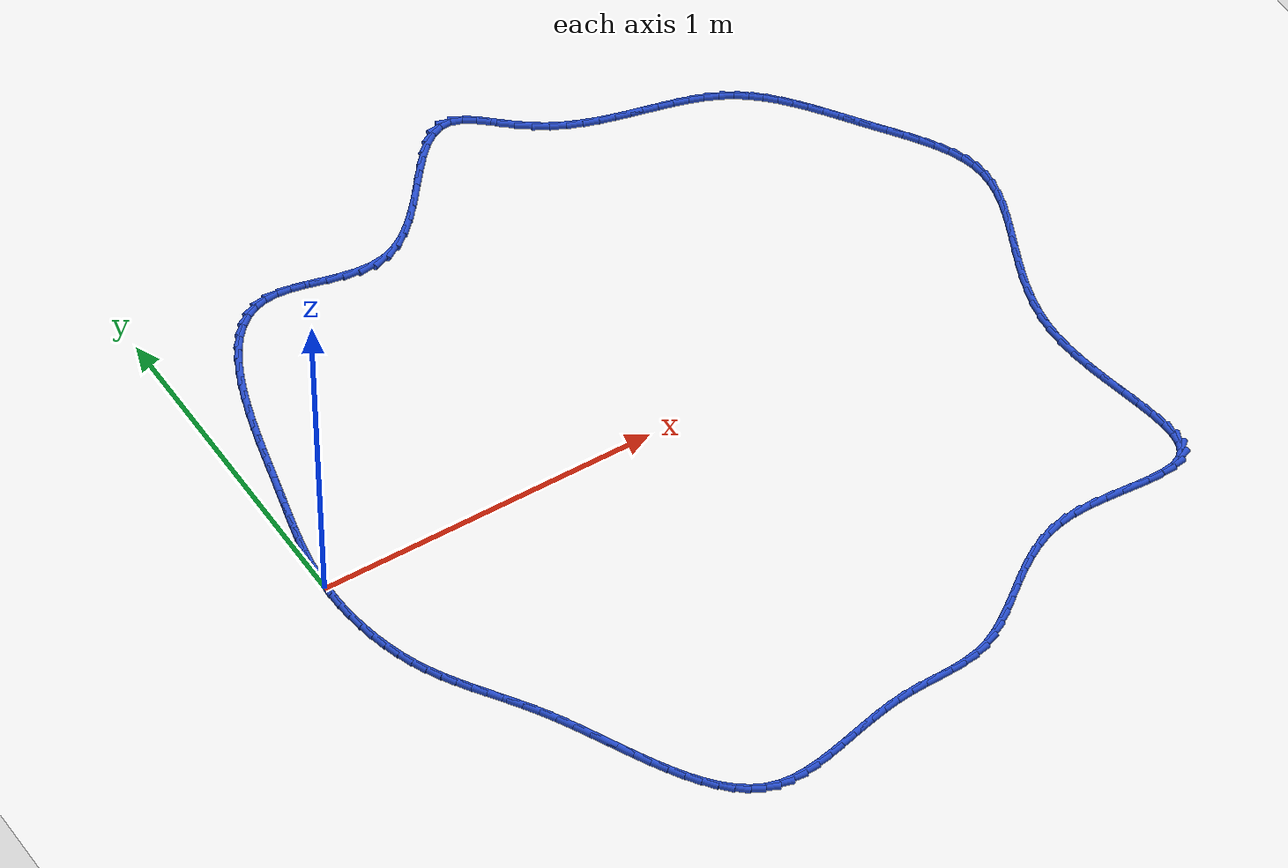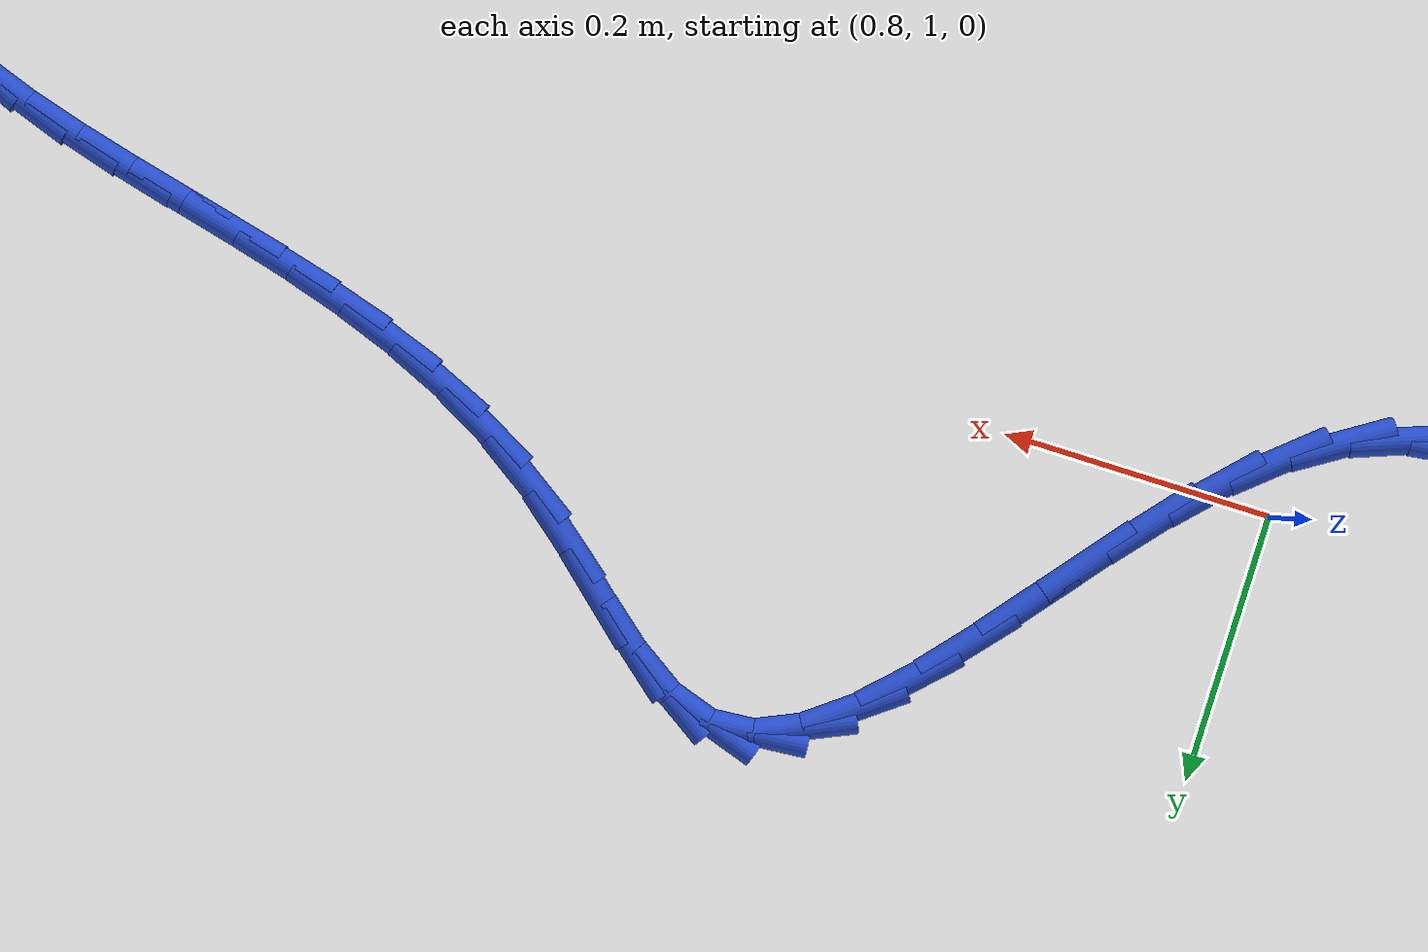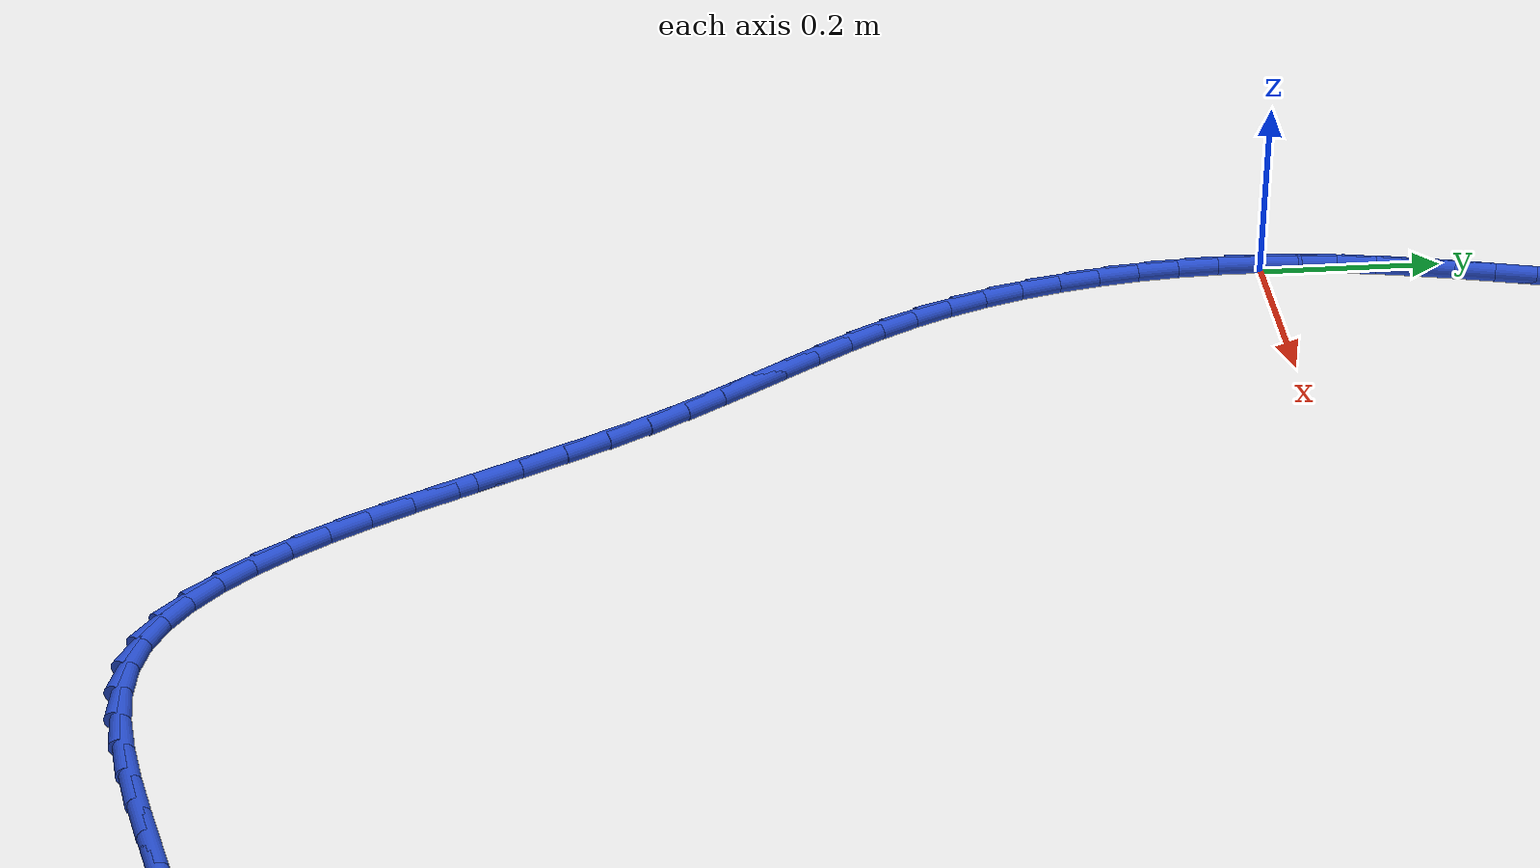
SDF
<sdf version="1.6">
 <world name="default">
  <light name="sun" type="directional">
   <pose>0 0 10 0 -0 0</pose>
   <diffuse>0.8 0.8 0.8 1</diffuse>
   <specular>0.2 0.2 0.2 1</specular>
   <attenuation>
    <range>1000</range>
    <constant>0.9</constant>
    <linear>0.01</linear>
    <quadratic>0.001</quadratic>
   </attenuation>
   <direction>-0.5 0.1 -0.9</direction>
  </light>
  <model name="ground_plane">
   <static>1</static>
   <link name="link">
    <collision name="collision">
     <geometry><plane><normal>0 0 1</normal><size>100 100</size></plane></geometry>
     <surface><friction><ode><mu>100</mu><mu2>50</mu2></ode></friction></surface>
    </collision>
    <visual name="visual">
     <cast_shadows>0</cast_shadows>
     <geometry><plane><normal>0 0 1</normal><size>100 100</size></plane></geometry>
     <material>
      <script><uri>file://media/materials/scripts/gazebo.material</uri><name>Gazebo/WhiteGlow</name></script>
     </material>
    </visual>
   </link>
  </model>
  <gravity>0 0 -9.8</gravity>
  <magnetic_field>6e-06 2.3e-05 -4.2e-05</magnetic_field>
  <atmosphere type="adiabatic"/>
  <physics name="default_physics" default="0" type="ode">
   <max_step_size>0.001</max_step_size>
   <real_time_factor>1</real_time_factor>
   <real_time_update_rate>1000</real_time_update_rate>
  </physics>
  <scene><ambient>0.4 0.4 0.4 1</ambient><background>0.7 0.7 0.7 1</background><shadows>1</shadows></scene>
  <spherical_coordinates>
   <surface_model>EARTH_WGS84</surface_model>
   <latitude_deg>0</latitude_deg>
   <longitude_deg>0</longitude_deg>
   <elevation>0</elevation>
   <heading_deg>0</heading_deg>
  </spherical_coordinates>
  <model name="line">
   <link name="link_0">
    <pose>-2.42861286636753e-17 1.3877787807814457e-17 0.01 0 1.57 1.5093590978031826</pose>
    <collision name="collision">
     <geometry><cylinder><radius>0.01</radius><length>0.08</length></cylinder></geometry>
    </collision>
    <visual name="visual">
     <material>
      <script><name>Gazebo/Blue</name><uri>file://media/materials/scripts/gazebo.material</uri></script>
     </material>
     <geometry><cylinder><radius>0.01</radius><length>0.08</length></cylinder></geometry>
    </visual>
   </link>
   <link name="link_1">
    <pose>0.0026496096669003204 0.04307282719865497 0.01 0 1.57 1.460139329362251</pose>
    <collision name="collision">
     <geometry><cylinder><radius>0.01</radius><length>0.08</length></cylinder></geometry>
    </collision>
    <visual name="visual">
     <material>
      <script><name>Gazebo/Blue</name><uri>file://media/materials/scripts/gazebo.material</uri></script>
     </material>
     <geometry><cylinder><radius>0.01</radius><length>0.08</length></cylinder></geometry>
    </visual>
   </link>
   <link name="link_2">
    <pose>0.007363580412355519 0.08549865039412194 0.01 0 1.57 1.4174308928001462</pose>
    <collision name="collision">
     <geometry><cylinder><radius>0.01</radius><length>0.08</length></cylinder></geometry>
    </collision>
    <visual name="visual">
     <material>
      <script><name>Gazebo/Blue</name><uri>file://media/materials/scripts/gazebo.material</uri></script>
     </material>
     <geometry><cylinder><radius>0.01</radius><length>0.08</length></cylinder></geometry>
    </visual>
   </link>
   <link name="link_3">
    <pose>0.01388491874355268 0.1276863092239814 0.01 0 1.57 1.3824960369768609</pose>
    <collision name="collision">
     <geometry><cylinder><radius>0.01</radius><length>0.08</length></cylinder></geometry>
    </collision>
    <visual name="visual">
     <material>
      <script><name>Gazebo/Blue</name><uri>file://media/materials/scripts/gazebo.material</uri></script>
     </material>
     <geometry><cylinder><radius>0.01</radius><length>0.08</length></cylinder></geometry>
    </visual>
   </link>
   <link name="link_4">
    <pose>0.021956631167678986 0.170044643325814 0.01 0 1.57 1.3560512879209734</pose>
    <collision name="collision">
     <geometry><cylinder><radius>0.01</radius><length>0.08</length></cylinder></geometry>
    </collision>
    <visual name="visual">
     <material>
      <script><name>Gazebo/Blue</name><uri>file://media/materials/scripts/gazebo.material</uri></script>
     </material>
     <geometry><cylinder><radius>0.01</radius><length>0.08</length></cylinder></geometry>
    </visual>
   </link>
   <link name="link_5">
    <pose>0.03132172419192152 0.21298249233720015 0.01 0 1.57 1.3382845328337616</pose>
    <collision name="collision">
     <geometry><cylinder><radius>0.01</radius><length>0.08</length></cylinder></geometry>
    </collision>
    <visual name="visual">
     <material>
      <script><name>Gazebo/Blue</name><uri>file://media/materials/scripts/gazebo.material</uri></script>
     </material>
     <geometry><cylinder><radius>0.01</radius><length>0.08</length></cylinder></geometry>
    </visual>
   </link>
   <link name="link_6">
    <pose>0.04172320432346745 0.2569086958957203 0.01 0 1.57 1.3289344449897182</pose>
    <collision name="collision">
     <geometry><cylinder><radius>0.01</radius><length>0.08</length></cylinder></geometry>
    </collision>
    <visual name="visual">
     <material>
      <script><name>Gazebo/Blue</name><uri>file://media/materials/scripts/gazebo.material</uri></script>
     </material>
     <geometry><cylinder><radius>0.01</radius><length>0.08</length></cylinder></geometry>
    </visual>
   </link>
   <link name="link_7">
    <pose>0.052904078069503924 0.3022320936389553 0.01 0 1.57 1.3273975969979865</pose>
    <collision name="collision">
     <geometry><cylinder><radius>0.01</radius><length>0.08</length></cylinder></geometry>
    </collision>
    <visual name="visual">
     <material>
      <script><name>Gazebo/Blue</name><uri>file://media/materials/scripts/gazebo.material</uri></script>
     </material>
     <geometry><cylinder><radius>0.01</radius><length>0.08</length></cylinder></geometry>
    </visual>
   </link>
   <link name="link_8">
    <pose>0.06460735193721806 0.3493615252044854 0.01 0 1.57 1.3318365359500797</pose>
    <collision name="collision">
     <geometry><cylinder><radius>0.01</radius><length>0.08</length></cylinder></geometry>
    </collision>
    <visual name="visual">
     <material>
      <script><name>Gazebo/Blue</name><uri>file://media/materials/scripts/gazebo.material</uri></script>
     </material>
     <geometry><cylinder><radius>0.01</radius><length>0.08</length></cylinder></geometry>
    </visual>
   </link>
   <link name="link_9">
    <pose>0.07660898984305621 0.3986264044124486 0.01 0 1.57 1.3332804026628118</pose>
    <collision name="collision">
     <geometry><cylinder><radius>0.01</radius><length>0.08</length></cylinder></geometry>
    </collision>
    <visual name="visual">
     <material>
      <script><name>Gazebo/Blue</name><uri>file://media/materials/scripts/gazebo.material</uri></script>
     </material>
     <geometry><cylinder><radius>0.01</radius><length>0.08</length></cylinder></geometry>
    </visual>
   </link>
   <link name="link_10">
    <pose>0.08896728992933452 0.44967573278160305 0.01 0 1.57 1.3279400840466655</pose>
    <collision name="collision">
     <geometry><cylinder><radius>0.01</radius><length>0.08</length></cylinder></geometry>
    </collision>
    <visual name="visual">
     <material>
      <script><name>Gazebo/Blue</name><uri>file://media/materials/scripts/gazebo.material</uri></script>
     </material>
     <geometry><cylinder><radius>0.01</radius><length>0.08</length></cylinder></geometry>
    </visual>
   </link>
   <link name="link_11">
    <pose>0.10188402960887925 0.5018127334882201 0.01 0 1.57 1.31604414092353</pose>
    <collision name="collision">
     <geometry><cylinder><radius>0.01</radius><length>0.08</length></cylinder></geometry>
    </collision>
    <visual name="visual">
     <material>
      <script><name>Gazebo/Blue</name><uri>file://media/materials/scripts/gazebo.material</uri></script>
     </material>
     <geometry><cylinder><radius>0.01</radius><length>0.08</length></cylinder></geometry>
    </visual>
   </link>
   <link name="link_12">
    <pose>0.11556211673399626 0.5543379054022088 0.01 0 1.57 1.2973886681237063</pose>
    <collision name="collision">
     <geometry><cylinder><radius>0.01</radius><length>0.08</length></cylinder></geometry>
    </collision>
    <visual name="visual">
     <material>
      <script><name>Gazebo/Blue</name><uri>file://media/materials/scripts/gazebo.material</uri></script>
     </material>
     <geometry><cylinder><radius>0.01</radius><length>0.08</length></cylinder></geometry>
    </visual>
   </link>
   <link name="link_13">
    <pose>0.13020445915699155 0.6065517473934785 0.01 0 1.57 1.2713211971521223</pose>
    <collision name="collision">
     <geometry><cylinder><radius>0.01</radius><length>0.08</length></cylinder></geometry>
    </collision>
    <visual name="visual">
     <material>
      <script><name>Gazebo/Blue</name><uri>file://media/materials/scripts/gazebo.material</uri></script>
     </material>
     <geometry><cylinder><radius>0.01</radius><length>0.08</length></cylinder></geometry>
    </visual>
   </link>
   <link name="link_14">
    <pose>0.14601396473017092 0.6577547583319379 0.01 0 1.57 1.2366953171147226</pose>
    <collision name="collision">
     <geometry><cylinder><radius>0.01</radius><length>0.08</length></cylinder></geometry>
    </collision>
    <visual name="visual">
     <material>
      <script><name>Gazebo/Blue</name><uri>file://media/materials/scripts/gazebo.material</uri></script>
     </material>
     <geometry><cylinder><radius>0.01</radius><length>0.08</length></cylinder></geometry>
    </visual>
   </link>
   <link name="link_15">
    <pose>0.16319354130584038 0.7072474370874962 0.01 0 1.57 1.1917662592871698</pose>
    <collision name="collision">
     <geometry><cylinder><radius>0.01</radius><length>0.08</length></cylinder></geometry>
    </collision>
    <visual name="visual">
     <material>
      <script><name>Gazebo/Blue</name><uri>file://media/materials/scripts/gazebo.material</uri></script>
     </material>
     <geometry><cylinder><radius>0.01</radius><length>0.08</length></cylinder></geometry>
    </visual>
   </link>
   <link name="link_16">
    <pose>0.1819460967363059 0.7543302825300626 0.01 0 1.57 1.13402967386434</pose>
    <collision name="collision">
     <geometry><cylinder><radius>0.01</radius><length>0.08</length></cylinder></geometry>
    </collision>
    <visual name="visual">
     <material>
      <script><name>Gazebo/Blue</name><uri>file://media/materials/scripts/gazebo.material</uri></script>
     </material>
     <geometry><cylinder><radius>0.01</radius><length>0.08</length></cylinder></geometry>
    </visual>
   </link>
   <link name="link_17">
    <pose>0.20247453887387334 0.7983037935295462 0.01 0 1.57 1.0600233958224863</pose>
    <collision name="collision">
     <geometry><cylinder><radius>0.01</radius><length>0.08</length></cylinder></geometry>
    </collision>
    <visual name="visual">
     <material>
      <script><name>Gazebo/Blue</name><uri>file://media/materials/scripts/gazebo.material</uri></script>
     </material>
     <geometry><cylinder><radius>0.01</radius><length>0.08</length></cylinder></geometry>
    </visual>
   </link>
   <link name="link_18">
    <pose>0.22498177557084853 0.8384684689558555 0.01 0 1.57 0.9651799736025226</pose>
    <collision name="collision">
     <geometry><cylinder><radius>0.01</radius><length>0.08</length></cylinder></geometry>
    </collision>
    <visual name="visual">
     <material>
      <script><name>Gazebo/Blue</name><uri>file://media/materials/scripts/gazebo.material</uri></script>
     </material>
     <geometry><cylinder><radius>0.01</radius><length>0.08</length></cylinder></geometry>
    </visual>
   </link>
   <link name="link_19">
    <pose>0.24967071467953755 0.8741248076789001 0.01 0 1.57 0.8440032859838902</pose>
    <collision name="collision">
     <geometry><cylinder><radius>0.01</radius><length>0.08</length></cylinder></geometry>
    </collision>
    <visual name="visual">
     <material>
      <script><name>Gazebo/Blue</name><uri>file://media/materials/scripts/gazebo.material</uri></script>
     </material>
     <geometry><cylinder><radius>0.01</radius><length>0.08</length></cylinder></geometry>
    </visual>
   </link>
   <link name="link_20">
    <pose>0.2767442640522463 0.9045733085685889 0.01 0 1.57 0.691218291757534</pose>
    <collision name="collision">
     <geometry><cylinder><radius>0.01</radius><length>0.08</length></cylinder></geometry>
    </collision>
    <visual name="visual">
     <material>
      <script><name>Gazebo/Blue</name><uri>file://media/materials/scripts/gazebo.material</uri></script>
     </material>
     <geometry><cylinder><radius>0.01</radius><length>0.08</length></cylinder></geometry>
    </visual>
   </link>
   <link name="link_21">
    <pose>0.3064053315412807 0.9291144704948312 0.01 0 1.57 0.5048755767474941</pose>
    <collision name="collision">
     <geometry><cylinder><radius>0.01</radius><length>0.08</length></cylinder></geometry>
    </collision>
    <visual name="visual">
     <material>
      <script><name>Gazebo/Blue</name><uri>file://media/materials/scripts/gazebo.material</uri></script>
     </material>
     <geometry><cylinder><radius>0.01</radius><length>0.08</length></cylinder></geometry>
    </visual>
   </link>
   <link name="link_22">
    <pose>0.3388568249989464 0.9470487923275355 0.01 0 1.57 0.29131526927594054</pose>
    <collision name="collision">
     <geometry><cylinder><radius>0.01</radius><length>0.08</length></cylinder></geometry>
    </collision>
    <visual name="visual">
     <material>
      <script><name>Gazebo/Blue</name><uri>file://media/materials/scripts/gazebo.material</uri></script>
     </material>
     <geometry><cylinder><radius>0.01</radius><length>0.08</length></cylinder></geometry>
    </visual>
   </link>
   <link name="link_23">
    <pose>0.37430165227754975 0.9576767729366116 0.01 0 1.57 0.06888097786250724</pose>
    <collision name="collision">
     <geometry><cylinder><radius>0.01</radius><length>0.08</length></cylinder></geometry>
    </collision>
    <visual name="visual">
     <material>
      <script><name>Gazebo/Blue</name><uri>file://media/materials/scripts/gazebo.material</uri></script>
     </material>
     <geometry><cylinder><radius>0.01</radius><length>0.08</length></cylinder></geometry>
    </visual>
   </link>
   <link name="link_24">
    <pose>0.4129302743863518 0.9603417663008713 0.01 0 1.57 -0.1087090265260488</pose>
    <collision name="collision">
     <geometry><cylinder><radius>0.01</radius><length>0.08</length></cylinder></geometry>
    </collision>
    <visual name="visual">
     <material>
      <script><name>Gazebo/Blue</name><uri>file://media/materials/scripts/gazebo.material</uri></script>
     </material>
     <geometry><cylinder><radius>0.01</radius><length>0.08</length></cylinder></geometry>
    </visual>
   </link>
   <link name="link_25">
    <pose>0.454522080896925 0.9558024661094408 0.01 0 1.57 -0.20859219315116076</pose>
    <collision name="collision">
     <geometry><cylinder><radius>0.01</radius><length>0.08</length></cylinder></geometry>
    </collision>
    <visual name="visual">
     <material>
      <script><name>Gazebo/Blue</name><uri>file://media/materials/scripts/gazebo.material</uri></script>
     </material>
     <geometry><cylinder><radius>0.01</radius><length>0.08</length></cylinder></geometry>
    </visual>
   </link>
   <link name="link_26">
    <pose>0.498361133587482 0.9465230046474837 0.01 0 1.57 -0.2474423943853463</pose>
    <collision name="collision">
     <geometry><cylinder><radius>0.01</radius><length>0.08</length></cylinder></geometry>
    </collision>
    <visual name="visual">
     <material>
      <script><name>Gazebo/Blue</name><uri>file://media/materials/scripts/gazebo.material</uri></script>
     </material>
     <geometry><cylinder><radius>0.01</radius><length>0.08</length></cylinder></geometry>
    </visual>
   </link>
   <link name="link_27">
    <pose>0.5437020122654131 0.9350690221139187 0.01 0 1.57 -0.23553503521103783</pose>
    <collision name="collision">
     <geometry><cylinder><radius>0.01</radius><length>0.08</length></cylinder></geometry>
    </collision>
    <visual name="visual">
     <material>
      <script><name>Gazebo/Blue</name><uri>file://media/materials/scripts/gazebo.material</uri></script>
     </material>
     <geometry><cylinder><radius>0.01</radius><length>0.08</length></cylinder></geometry>
    </visual>
   </link>
   <link name="link_28">
    <pose>0.5897992967381088 0.9240061587076634 0.01 0 1.57 -0.17402747333654878</pose>
    <collision name="collision">
     <geometry><cylinder><radius>0.01</radius><length>0.08</length></cylinder></geometry>
    </collision>
    <visual name="visual">
     <material>
      <script><name>Gazebo/Blue</name><uri>file://media/materials/scripts/gazebo.material</uri></script>
     </material>
     <geometry><cylinder><radius>0.01</radius><length>0.08</length></cylinder></geometry>
    </visual>
   </link>
   <link name="link_29">
    <pose>0.6359075668129591 0.9159000546276366 0.01 0 1.57 -0.05688118333882828</pose>
    <collision name="collision">
     <geometry><cylinder><radius>0.01</radius><length>0.08</length></cylinder></geometry>
    </collision>
    <visual name="visual">
     <material>
      <script><name>Gazebo/Blue</name><uri>file://media/materials/scripts/gazebo.material</uri></script>
     </material>
     <geometry><cylinder><radius>0.01</radius><length>0.08</length></cylinder></geometry>
    </visual>
   </link>
   <link name="link_30">
    <pose>0.6812814022973541 0.9133163500727559 0.01 0 1.57 0.12474949393419657</pose>
    <collision name="collision">
     <geometry><cylinder><radius>0.01</radius><length>0.08</length></cylinder></geometry>
    </collision>
    <visual name="visual">
     <material>
      <script><name>Gazebo/Blue</name><uri>file://media/materials/scripts/gazebo.material</uri></script>
     </material>
     <geometry><cylinder><radius>0.01</radius><length>0.08</length></cylinder></geometry>
    </visual>
   </link>
   <link name="link_31">
    <pose>0.7251753829986847 0.9188206852419399 0.01 0 1.57 0.36061511473032476</pose>
    <collision name="collision">
     <geometry><cylinder><radius>0.01</radius><length>0.08</length></cylinder></geometry>
    </collision>
    <visual name="visual">
     <material>
      <script><name>Gazebo/Blue</name><uri>file://media/materials/scripts/gazebo.material</uri></script>
     </material>
     <geometry><cylinder><radius>0.01</radius><length>0.08</length></cylinder></geometry>
    </visual>
   </link>
   <link name="link_32">
    <pose>0.7669325696557691 0.9345675407247536 0.01 0 1.57 0.5662187043159957</pose>
    <collision name="collision">
     <geometry><cylinder><radius>0.01</radius><length>0.08</length></cylinder></geometry>
    </collision>
    <visual name="visual">
     <material>
      <script><name>Gazebo/Blue</name><uri>file://media/materials/scripts/gazebo.material</uri></script>
     </material>
     <geometry><cylinder><radius>0.01</radius><length>0.08</length></cylinder></geometry>
    </visual>
   </link>
   <link name="link_33">
    <pose>0.8065352765329802 0.9597408674655573 0.01 0 1.57 0.7109833255921929</pose>
    <collision name="collision">
     <geometry><cylinder><radius>0.01</radius><length>0.08</length></cylinder></geometry>
    </collision>
    <visual name="visual">
     <material>
      <script><name>Gazebo/Blue</name><uri>file://media/materials/scripts/gazebo.material</uri></script>
     </material>
     <geometry><cylinder><radius>0.01</radius><length>0.08</length></cylinder></geometry>
    </visual>
   </link>
   <link name="link_34">
    <pose>0.8442466895998031 0.9922194413988233 0.01 0 1.57 0.8067189992806727</pose>
    <collision name="collision">
     <geometry><cylinder><radius>0.01</radius><length>0.08</length></cylinder></geometry>
    </collision>
    <visual name="visual">
     <material>
      <script><name>Gazebo/Blue</name><uri>file://media/materials/scripts/gazebo.material</uri></script>
     </material>
     <geometry><cylinder><radius>0.01</radius><length>0.08</length></cylinder></geometry>
    </visual>
   </link>
   <link name="link_35">
    <pose>0.8803312031458321 1.0298764235495068 0.01 0 1.57 0.8645971121159285</pose>
    <collision name="collision">
     <geometry><cylinder><radius>0.01</radius><length>0.08</length></cylinder></geometry>
    </collision>
    <visual name="visual">
     <material>
      <script><name>Gazebo/Blue</name><uri>file://media/materials/scripts/gazebo.material</uri></script>
     </material>
     <geometry><cylinder><radius>0.01</radius><length>0.08</length></cylinder></geometry>
    </visual>
   </link>
   <link name="link_36">
    <pose>0.9150532114606617 1.0705849749425616 0.01 0 1.57 0.8914258986588142</pose>
    <collision name="collision">
     <geometry><cylinder><radius>0.01</radius><length>0.08</length></cylinder></geometry>
    </collision>
    <visual name="visual">
     <material>
      <script><name>Gazebo/Blue</name><uri>file://media/materials/scripts/gazebo.material</uri></script>
     </material>
     <geometry><cylinder><radius>0.01</radius><length>0.08</length></cylinder></geometry>
    </visual>
   </link>
   <link name="link_37">
    <pose>0.9486771088338859 1.1122182566029424 0.01 0 1.57 0.8893765129638842</pose>
    <collision name="collision">
     <geometry><cylinder><radius>0.01</radius><length>0.08</length></cylinder></geometry>
    </collision>
    <visual name="visual">
     <material>
      <script><name>Gazebo/Blue</name><uri>file://media/materials/scripts/gazebo.material</uri></script>
     </material>
     <geometry><cylinder><radius>0.01</radius><length>0.08</length></cylinder></geometry>
    </visual>
   </link>
   <link name="link_38">
    <pose>0.9814672895550991 1.1526494295556033 0.01 0 1.57 0.8556968707887486</pose>
    <collision name="collision">
     <geometry><cylinder><radius>0.01</radius><length>0.08</length></cylinder></geometry>
    </collision>
    <visual name="visual">
     <material>
      <script><name>Gazebo/Blue</name><uri>file://media/materials/scripts/gazebo.material</uri></script>
     </material>
     <geometry><cylinder><radius>0.01</radius><length>0.08</length></cylinder></geometry>
    </visual>
   </link>
   <link name="link_39">
    <pose>1.013688147913896 1.1897516548254996 0.01 0 1.57 0.7811583897106996</pose>
    <collision name="collision">
     <geometry><cylinder><radius>0.01</radius><length>0.08</length></cylinder></geometry>
    </collision>
    <visual name="visual">
     <material>
      <script><name>Gazebo/Blue</name><uri>file://media/materials/scripts/gazebo.material</uri></script>
     </material>
     <geometry><cylinder><radius>0.01</radius><length>0.08</length></cylinder></geometry>
    </visual>
   </link>
   <link name="link_40">
    <pose>1.04560407819987 1.2213980934375848 0.01 0 1.57 0.6466512454995315</pose>
    <collision name="collision">
     <geometry><cylinder><radius>0.01</radius><length>0.08</length></cylinder></geometry>
    </collision>
    <visual name="visual">
     <material>
      <script><name>Gazebo/Blue</name><uri>file://media/materials/scripts/gazebo.material</uri></script>
     </material>
     <geometry><cylinder><radius>0.01</radius><length>0.08</length></cylinder></geometry>
    </visual>
   </link>
   <link name="link_41">
    <pose>1.0774794747026155 1.2454619064168135 0.01 0 1.57 0.42051159910092095</pose>
    <collision name="collision">
     <geometry><cylinder><radius>0.01</radius><length>0.08</length></cylinder></geometry>
    </collision>
    <visual name="visual">
     <material>
      <script><name>Gazebo/Blue</name><uri>file://media/materials/scripts/gazebo.material</uri></script>
     </material>
     <geometry><cylinder><radius>0.01</radius><length>0.08</length></cylinder></geometry>
    </visual>
   </link>
   <link name="link_42">
    <pose>1.1095787317117276 1.2598162547881409 0.01 0 1.57 0.07711700090607639</pose>
    <collision name="collision">
     <geometry><cylinder><radius>0.01</radius><length>0.08</length></cylinder></geometry>
    </collision>
    <visual name="visual">
     <material>
      <script><name>Gazebo/Blue</name><uri>file://media/materials/scripts/gazebo.material</uri></script>
     </material>
     <geometry><cylinder><radius>0.01</radius><length>0.08</length></cylinder></geometry>
    </visual>
   </link>
   <link name="link_43">
    <pose>1.1421662435167996 1.262334299576521 0.01 0 1.57 -0.3197321535231422</pose>
    <collision name="collision">
     <geometry><cylinder><radius>0.01</radius><length>0.08</length></cylinder></geometry>
    </collision>
    <visual name="visual">
     <material>
      <script><name>Gazebo/Blue</name><uri>file://media/materials/scripts/gazebo.material</uri></script>
     </material>
     <geometry><cylinder><radius>0.01</radius><length>0.08</length></cylinder></geometry>
    </visual>
   </link>
   <link name="link_44">
    <pose>1.1755025355176567 1.2512969143012802 0.01 0 1.57 -0.5799717321479565</pose>
    <collision name="collision">
     <geometry><cylinder><radius>0.01</radius><length>0.08</length></cylinder></geometry>
    </collision>
    <visual name="visual">
     <material>
      <script><name>Gazebo/Blue</name><uri>file://media/materials/scripts/gazebo.material</uri></script>
     </material>
     <geometry><cylinder><radius>0.01</radius><length>0.08</length></cylinder></geometry>
    </visual>
   </link>
   <link name="link_45">
    <pose>1.209811741626421 1.2288199910815454 0.01 0 1.57 -0.6968246334765356</pose>
    <collision name="collision">
     <geometry><cylinder><radius>0.01</radius><length>0.08</length></cylinder></geometry>
    </collision>
    <visual name="visual">
     <material>
      <script><name>Gazebo/Blue</name><uri>file://media/materials/scripts/gazebo.material</uri></script>
     </material>
     <geometry><cylinder><radius>0.01</radius><length>0.08</length></cylinder></geometry>
    </visual>
   </link>
   <link name="link_46">
    <pose>1.2452980400003082 1.1991224053455214 0.01 0 1.57 -0.7252281345553646</pose>
    <collision name="collision">
     <geometry><cylinder><radius>0.01</radius><length>0.08</length></cylinder></geometry>
    </collision>
    <visual name="visual">
     <material>
      <script><name>Gazebo/Blue</name><uri>file://media/materials/scripts/gazebo.material</uri></script>
     </material>
     <geometry><cylinder><radius>0.01</radius><length>0.08</length></cylinder></geometry>
    </visual>
   </link>
   <link name="link_47">
    <pose>1.2821654038363102 1.1664446317009598 0.01 0 1.57 -0.6850529834486366</pose>
    <collision name="collision">
     <geometry><cylinder><radius>0.01</radius><length>0.08</length></cylinder></geometry>
    </collision>
    <visual name="visual">
     <material>
      <script><name>Gazebo/Blue</name><uri>file://media/materials/scripts/gazebo.material</uri></script>
     </material>
     <geometry><cylinder><radius>0.01</radius><length>0.08</length></cylinder></geometry>
    </visual>
   </link>
   <link name="link_48">
    <pose>1.32061779022801 1.135026992760359 0.01 0 1.57 -0.5902988109571177</pose>
    <collision name="collision">
     <geometry><cylinder><radius>0.01</radius><length>0.08</length></cylinder></geometry>
    </collision>
    <visual name="visual">
     <material>
      <script><name>Gazebo/Blue</name><uri>file://media/materials/scripts/gazebo.material</uri></script>
     </material>
     <geometry><cylinder><radius>0.01</radius><length>0.08</length></cylinder></geometry>
    </visual>
   </link>
   <link name="link_49">
    <pose>1.3607558717823172 1.1081349396417972 0.01 0 1.57 -0.49401061503865684</pose>
    <collision name="collision">
     <geometry><cylinder><radius>0.01</radius><length>0.08</length></cylinder></geometry>
    </collision>
    <visual name="visual">
     <material>
      <script><name>Gazebo/Blue</name><uri>file://media/materials/scripts/gazebo.material</uri></script>
     </material>
     <geometry><cylinder><radius>0.01</radius><length>0.08</length></cylinder></geometry>
    </visual>
   </link>
   <link name="link_50">
    <pose>1.4023317850599142 1.085744195575143 0.01 0 1.57 -0.4110133203528333</pose>
    <collision name="collision">
     <geometry><cylinder><radius>0.01</radius><length>0.08</length></cylinder></geometry>
    </collision>
    <visual name="visual">
     <material>
      <script><name>Gazebo/Blue</name><uri>file://media/materials/scripts/gazebo.material</uri></script>
     </material>
     <geometry><cylinder><radius>0.01</radius><length>0.08</length></cylinder></geometry>
    </visual>
   </link>
   <link name="link_51">
    <pose>1.4450242232540627 1.0671372737288356 0.01 0 1.57 -0.3432131948759112</pose>
    <collision name="collision">
     <geometry><cylinder><radius>0.01</radius><length>0.08</length></cylinder></geometry>
    </collision>
    <visual name="visual">
     <material>
      <script><name>Gazebo/Blue</name><uri>file://media/materials/scripts/gazebo.material</uri></script>
     </material>
     <geometry><cylinder><radius>0.01</radius><length>0.08</length></cylinder></geometry>
    </visual>
   </link>
   <link name="link_52">
    <pose>1.4885118795580246 1.0515966872713136 0.01 0 1.57 -0.2915249848013818</pose>
    <collision name="collision">
     <geometry><cylinder><radius>0.01</radius><length>0.08</length></cylinder></geometry>
    </collision>
    <visual name="visual">
     <material>
      <script><name>Gazebo/Blue</name><uri>file://media/materials/scripts/gazebo.material</uri></script>
     </material>
     <geometry><cylinder><radius>0.01</radius><length>0.08</length></cylinder></geometry>
    </visual>
   </link>
   <link name="link_53">
    <pose>1.5324734471650612 1.0384049493710177 0.01 0 1.57 -0.2562927522322494</pose>
    <collision name="collision">
     <geometry><cylinder><radius>0.01</radius><length>0.08</length></cylinder></geometry>
    </collision>
    <visual name="visual">
     <material>
      <script><name>Gazebo/Blue</name><uri>file://media/materials/scripts/gazebo.material</uri></script>
     </material>
     <geometry><cylinder><radius>0.01</radius><length>0.08</length></cylinder></geometry>
    </visual>
   </link>
   <link name="link_54">
    <pose>1.5765876192684334 1.0268445731963858 0.01 0 1.57 -0.2376866372476625</pose>
    <collision name="collision">
     <geometry><cylinder><radius>0.01</radius><length>0.08</length></cylinder></geometry>
    </collision>
    <visual name="visual">
     <material>
      <script><name>Gazebo/Blue</name><uri>file://media/materials/scripts/gazebo.material</uri></script>
     </material>
     <geometry><cylinder><radius>0.01</radius><length>0.08</length></cylinder></geometry>
    </visual>
   </link>
   <link name="link_55">
    <pose>1.6205330890614036 1.0161980719158576 0.01 0 1.57 -0.23599757157807744</pose>
    <collision name="collision">
     <geometry><cylinder><radius>0.01</radius><length>0.08</length></cylinder></geometry>
    </collision>
    <visual name="visual">
     <material>
      <script><name>Gazebo/Blue</name><uri>file://media/materials/scripts/gazebo.material</uri></script>
     </material>
     <geometry><cylinder><radius>0.01</radius><length>0.08</length></cylinder></geometry>
    </visual>
   </link>
   <link name="link_56">
    <pose>1.6639885497372324 1.0057479586978726 0.01 0 1.57 -0.25181258754173313</pose>
    <collision name="collision">
     <geometry><cylinder><radius>0.01</radius><length>0.08</length></cylinder></geometry>
    </collision>
    <visual name="visual">
     <material>
      <script><name>Gazebo/Blue</name><uri>file://media/materials/scripts/gazebo.material</uri></script>
     </material>
     <geometry><cylinder><radius>0.01</radius><length>0.08</length></cylinder></geometry>
    </visual>
   </link>
   <link name="link_57">
    <pose>1.7066326944891816 0.9947767467108699 0.01 0 1.57 -0.28606311298198234</pose>
    <collision name="collision">
     <geometry><cylinder><radius>0.01</radius><length>0.08</length></cylinder></geometry>
    </collision>
    <visual name="visual">
     <material>
      <script><name>Gazebo/Blue</name><uri>file://media/materials/scripts/gazebo.material</uri></script>
     </material>
     <geometry><cylinder><radius>0.01</radius><length>0.08</length></cylinder></geometry>
    </visual>
   </link>
   <link name="link_58">
    <pose>1.7481442165105134 0.9825669491232889 0.01 0 1.57 -0.33991174146069714</pose>
    <collision name="collision">
     <geometry><cylinder><radius>0.01</radius><length>0.08</length></cylinder></geometry>
    </collision>
    <visual name="visual">
     <material>
      <script><name>Gazebo/Blue</name><uri>file://media/materials/scripts/gazebo.material</uri></script>
     </material>
     <geometry><cylinder><radius>0.01</radius><length>0.08</length></cylinder></geometry>
    </visual>
   </link>
   <link name="link_59">
    <pose>1.7882018089944887 0.968401079103569 0.01 0 1.57 -0.4144016603427869</pose>
    <collision name="collision">
     <geometry><cylinder><radius>0.01</radius><length>0.08</length></cylinder></geometry>
    </collision>
    <visual name="visual">
     <material>
      <script><name>Gazebo/Blue</name><uri>file://media/materials/scripts/gazebo.material</uri></script>
     </material>
     <geometry><cylinder><radius>0.01</radius><length>0.08</length></cylinder></geometry>
    </visual>
   </link>
   <link name="link_60">
    <pose>1.8264841651343686 0.9515616498201493 0.01 0 1.57 -0.509780699336614</pose>
    <collision name="collision">
     <geometry><cylinder><radius>0.01</radius><length>0.08</length></cylinder></geometry>
    </collision>
    <visual name="visual">
     <material>
      <script><name>Gazebo/Blue</name><uri>file://media/materials/scripts/gazebo.material</uri></script>
     </material>
     <geometry><cylinder><radius>0.01</radius><length>0.08</length></cylinder></geometry>
    </visual>
   </link>
   <link name="link_61">
    <pose>1.8626699964901778 0.9313312068680716 0.01 0 1.57 -0.6181137366673775</pose>
    <collision name="collision">
     <geometry><cylinder><radius>0.01</radius><length>0.08</length></cylinder></geometry>
    </collision>
    <visual name="visual">
     <material>
      <script><name>Gazebo/Blue</name><uri>file://media/materials/scripts/gazebo.material</uri></script>
     </material>
     <geometry><cylinder><radius>0.01</radius><length>0.08</length></cylinder></geometry>
    </visual>
   </link>
   <link name="link_62">
    <pose>1.8965703138603482 0.9072258707457962 0.01 0 1.57 -0.7149017972623273</pose>
    <collision name="collision">
     <geometry><cylinder><radius>0.01</radius><length>0.08</length></cylinder></geometry>
    </collision>
    <visual name="visual">
     <material>
      <script><name>Gazebo/Blue</name><uri>file://media/materials/scripts/gazebo.material</uri></script>
     </material>
     <geometry><cylinder><radius>0.01</radius><length>0.08</length></cylinder></geometry>
    </visual>
   </link>
   <link name="link_63">
    <pose>1.9284456041572378 0.8795553140626048 0.01 0 1.57 -0.794446242574055</pose>
    <collision name="collision">
     <geometry><cylinder><radius>0.01</radius><length>0.08</length></cylinder></geometry>
    </collision>
    <visual name="visual">
     <material>
      <script><name>Gazebo/Blue</name><uri>file://media/materials/scripts/gazebo.material</uri></script>
     </material>
     <geometry><cylinder><radius>0.01</radius><length>0.08</length></cylinder></geometry>
    </visual>
   </link>
   <link name="link_64">
    <pose>1.9586517197801137 0.8487975776259856 0.01 0 1.57 -0.8571364872842282</pose>
    <collision name="collision">
     <geometry><cylinder><radius>0.01</radius><length>0.08</length></cylinder></geometry>
    </collision>
    <visual name="visual">
     <material>
      <script><name>Gazebo/Blue</name><uri>file://media/materials/scripts/gazebo.material</uri></script>
     </material>
     <geometry><cylinder><radius>0.01</radius><length>0.08</length></cylinder></geometry>
    </visual>
   </link>
   <link name="link_65">
    <pose>1.987544513128244 0.8154307022434258 0.01 0 1.57 -0.9040601488476946</pose>
    <collision name="collision">
     <geometry><cylinder><radius>0.01</radius><length>0.08</length></cylinder></geometry>
    </collision>
    <visual name="visual">
     <material>
      <script><name>Gazebo/Blue</name><uri>file://media/materials/scripts/gazebo.material</uri></script>
     </material>
     <geometry><cylinder><radius>0.01</radius><length>0.08</length></cylinder></geometry>
    </visual>
   </link>
   <link name="link_66">
    <pose>2.015479836600899 0.7799327287224133 0.01 0 1.57 -0.9364806510068215</pose>
    <collision name="collision">
     <geometry><cylinder><radius>0.01</radius><length>0.08</length></cylinder></geometry>
    </collision>
    <visual name="visual">
     <material>
      <script><name>Gazebo/Blue</name><uri>file://media/materials/scripts/gazebo.material</uri></script>
     </material>
     <geometry><cylinder><radius>0.01</radius><length>0.08</length></cylinder></geometry>
    </visual>
   </link>
   <link name="link_67">
    <pose>2.042813542597344 0.7427816978704356 0.01 0 1.57 -0.9555369913048907</pose>
    <collision name="collision">
     <geometry><cylinder><radius>0.01</radius><length>0.08</length></cylinder></geometry>
    </collision>
    <visual name="visual">
     <material>
      <script><name>Gazebo/Blue</name><uri>file://media/materials/scripts/gazebo.material</uri></script>
     </material>
     <geometry><cylinder><radius>0.01</radius><length>0.08</length></cylinder></geometry>
    </visual>
   </link>
   <link name="link_68">
    <pose>2.0699014835168503 0.70445565049498 0.01 0 1.57 -0.9621041966814047</pose>
    <collision name="collision">
     <geometry><cylinder><radius>0.01</radius><length>0.08</length></cylinder></geometry>
    </collision>
    <visual name="visual">
     <material>
      <script><name>Gazebo/Blue</name><uri>file://media/materials/scripts/gazebo.material</uri></script>
     </material>
     <geometry><cylinder><radius>0.01</radius><length>0.08</length></cylinder></geometry>
    </visual>
   </link>
   <link name="link_69">
    <pose>2.0970995117586844 0.665432627403535 0.01 0 1.57 -0.9568245823652092</pose>
    <collision name="collision">
     <geometry><cylinder><radius>0.01</radius><length>0.08</length></cylinder></geometry>
    </collision>
    <visual name="visual">
     <material>
      <script><name>Gazebo/Blue</name><uri>file://media/materials/scripts/gazebo.material</uri></script>
     </material>
     <geometry><cylinder><radius>0.01</radius><length>0.08</length></cylinder></geometry>
    </visual>
   </link>
   <link name="link_70">
    <pose>2.124759990577584 0.626189402555078 0.01 0 1.57 -0.9489674352968395</pose>
    <collision name="collision">
     <geometry><cylinder><radius>0.01</radius><length>0.08</length></cylinder></geometry>
    </collision>
    <visual name="visual">
     <material>
      <script><name>Gazebo/Blue</name><uri>file://media/materials/scripts/gazebo.material</uri></script>
     </material>
     <geometry><cylinder><radius>0.01</radius><length>0.08</length></cylinder></geometry>
    </visual>
   </link>
   <link name="link_71">
    <pose>2.1528110794987487 0.5870487288131705 0.01 0 1.57 -0.9560482250160006</pose>
    <collision name="collision">
     <geometry><cylinder><radius>0.01</radius><length>0.08</length></cylinder></geometry>
    </collision>
    <visual name="visual">
     <material>
      <script><name>Gazebo/Blue</name><uri>file://media/materials/scripts/gazebo.material</uri></script>
     </material>
     <geometry><cylinder><radius>0.01</radius><length>0.08</length></cylinder></geometry>
    </visual>
   </link>
   <link name="link_72">
    <pose>2.180355984089364 0.5480338324143506 0.01 0 1.57 -0.9807779527962058</pose>
    <collision name="collision">
     <geometry><cylinder><radius>0.01</radius><length>0.08</length></cylinder></geometry>
    </collision>
    <visual name="visual">
     <material>
      <script><name>Gazebo/Blue</name><uri>file://media/materials/scripts/gazebo.material</uri></script>
     </material>
     <geometry><cylinder><radius>0.01</radius><length>0.08</length></cylinder></geometry>
    </visual>
   </link>
   <link name="link_73">
    <pose>2.2064029760622654 0.5091334707415812 0.01 0 1.57 -1.0251038445130498</pose>
    <collision name="collision">
     <geometry><cylinder><radius>0.01</radius><length>0.08</length></cylinder></geometry>
    </collision>
    <visual name="visual">
     <material>
      <script><name>Gazebo/Blue</name><uri>file://media/materials/scripts/gazebo.material</uri></script>
     </material>
     <geometry><cylinder><radius>0.01</radius><length>0.08</length></cylinder></geometry>
    </visual>
   </link>
   <link name="link_74">
    <pose>2.2299603271302892 0.4703364011778246 0.01 0 1.57 -1.0923072317085598</pose>
    <collision name="collision">
     <geometry><cylinder><radius>0.01</radius><length>0.08</length></cylinder></geometry>
    </collision>
    <visual name="visual">
     <material>
      <script><name>Gazebo/Blue</name><uri>file://media/materials/scripts/gazebo.material</uri></script>
     </material>
     <geometry><cylinder><radius>0.01</radius><length>0.08</length></cylinder></geometry>
    </visual>
   </link>
   <link name="link_75">
    <pose>2.2500363090062714 0.4316313811060451 0.01 0 1.57 -1.186875322030566</pose>
    <collision name="collision">
     <geometry><cylinder><radius>0.01</radius><length>0.08</length></cylinder></geometry>
    </collision>
    <visual name="visual">
     <material>
      <script><name>Gazebo/Blue</name><uri>file://media/materials/scripts/gazebo.material</uri></script>
     </material>
     <geometry><cylinder><radius>0.01</radius><length>0.08</length></cylinder></geometry>
    </visual>
   </link>
   <link name="link_76">
    <pose>2.2656391934030475 0.3930071679092051 0.01 0 1.57 -1.3136638419676914</pose>
    <collision name="collision">
     <geometry><cylinder><radius>0.01</radius><length>0.08</length></cylinder></geometry>
    </collision>
    <visual name="visual">
     <material>
      <script><name>Gazebo/Blue</name><uri>file://media/materials/scripts/gazebo.material</uri></script>
     </material>
     <geometry><cylinder><radius>0.01</radius><length>0.08</length></cylinder></geometry>
    </visual>
   </link>
   <link name="link_77">
    <pose>2.2757772710103135 0.3544525176121599 0.01 0 1.57 -1.4669121684383677</pose>
    <collision name="collision">
     <geometry><cylinder><radius>0.01</radius><length>0.08</length></cylinder></geometry>
    </collision>
    <visual name="visual">
     <material>
      <script><name>Gazebo/Blue</name><uri>file://media/materials/scripts/gazebo.material</uri></script>
     </material>
     <geometry><cylinder><radius>0.01</radius><length>0.08</length></cylinder></geometry>
    </visual>
   </link>
   <link name="link_78">
    <pose>2.2797933747505494 0.31593224422186766 0.01 0 1.57 1.530002082927227</pose>
    <collision name="collision">
     <geometry><cylinder><radius>0.01</radius><length>0.08</length></cylinder></geometry>
    </collision>
    <visual name="visual">
     <material>
      <script><name>Gazebo/Blue</name><uri>file://media/materials/scripts/gazebo.material</uri></script>
     </material>
     <geometry><cylinder><radius>0.01</radius><length>0.08</length></cylinder></geometry>
    </visual>
   </link>
   <link name="link_79">
    <pose>2.2782175958970687 0.27732619381627677 0.01 0 1.57 1.4080914340890538</pose>
    <collision name="collision">
     <geometry><cylinder><radius>0.01</radius><length>0.08</length></cylinder></geometry>
    </collision>
    <visual name="visual">
     <material>
      <script><name>Gazebo/Blue</name><uri>file://media/materials/scripts/gazebo.material</uri></script>
     </material>
     <geometry><cylinder><radius>0.01</radius><length>0.08</length></cylinder></geometry>
    </visual>
   </link>
   <link name="link_80">
    <pose>2.2718432828781374 0.23849537207921634 0.01 0 1.57 1.3119190758557582</pose>
    <collision name="collision">
     <geometry><cylinder><radius>0.01</radius><length>0.08</length></cylinder></geometry>
    </collision>
    <visual name="visual">
     <material>
      <script><name>Gazebo/Blue</name><uri>file://media/materials/scripts/gazebo.material</uri></script>
     </material>
     <geometry><cylinder><radius>0.01</radius><length>0.08</length></cylinder></geometry>
    </visual>
   </link>
   <link name="link_81">
    <pose>2.2614637841220224 0.19930078469451434 0.01 0 1.57 1.24093143862239</pose>
    <collision name="collision">
     <geometry><cylinder><radius>0.01</radius><length>0.08</length></cylinder></geometry>
    </collision>
    <visual name="visual">
     <material>
      <script><name>Gazebo/Blue</name><uri>file://media/materials/scripts/gazebo.material</uri></script>
     </material>
     <geometry><cylinder><radius>0.01</radius><length>0.08</length></cylinder></geometry>
    </visual>
   </link>
   <link name="link_82">
    <pose>2.247872448056989 0.15960343734599866 0.01 0 1.57 1.1929815894317892</pose>
    <collision name="collision">
     <geometry><cylinder><radius>0.01</radius><length>0.08</length></cylinder></geometry>
    </collision>
    <visual name="visual">
     <material>
      <script><name>Gazebo/Blue</name><uri>file://media/materials/scripts/gazebo.material</uri></script>
     </material>
     <geometry><cylinder><radius>0.01</radius><length>0.08</length></cylinder></geometry>
    </visual>
   </link>
   <link name="link_83">
    <pose>2.2318626231113043 0.11926433571749842 0.01 0 1.57 1.1656544784432366</pose>
    <collision name="collision">
     <geometry><cylinder><radius>0.01</radius><length>0.08</length></cylinder></geometry>
    </collision>
    <visual name="visual">
     <material>
      <script><name>Gazebo/Blue</name><uri>file://media/materials/scripts/gazebo.material</uri></script>
     </material>
     <geometry><cylinder><radius>0.01</radius><length>0.08</length></cylinder></geometry>
    </visual>
   </link>
   <link name="link_84">
    <pose>2.214227657713234 0.07814448549284116 0.01 0 1.57 1.1569007065667807</pose>
    <collision name="collision">
     <geometry><cylinder><radius>0.01</radius><length>0.08</length></cylinder></geometry>
    </collision>
    <visual name="visual">
     <material>
      <script><name>Gazebo/Blue</name><uri>file://media/materials/scripts/gazebo.material</uri></script>
     </material>
     <geometry><cylinder><radius>0.01</radius><length>0.08</length></cylinder></geometry>
    </visual>
   </link>
   <link name="link_85">
    <pose>2.195760900291045 0.03610489235585602 0.01 0 1.57 1.1652286912748988</pose>
    <collision name="collision">
     <geometry><cylinder><radius>0.01</radius><length>0.08</length></cylinder></geometry>
    </collision>
    <visual name="visual">
     <material>
      <script><name>Gazebo/Blue</name><uri>file://media/materials/scripts/gazebo.material</uri></script>
     </material>
     <geometry><cylinder><radius>0.01</radius><length>0.08</length></cylinder></geometry>
    </visual>
   </link>
   <link name="link_86">
    <pose>2.177255699273004 -0.006993438009629024 0.01 0 1.57 1.1896698371130612</pose>
    <collision name="collision">
     <geometry><cylinder><radius>0.01</radius><length>0.08</length></cylinder></geometry>
    </collision>
    <visual name="visual">
     <material>
      <script><name>Gazebo/Blue</name><uri>file://media/materials/scripts/gazebo.material</uri></script>
     </material>
     <geometry><cylinder><radius>0.01</radius><length>0.08</length></cylinder></geometry>
    </visual>
   </link>
   <link name="link_87">
    <pose>2.159505403087377 -0.05128949991978565 0.01 0 1.57 1.229627357101661</pose>
    <collision name="collision">
     <geometry><cylinder><radius>0.01</radius><length>0.08</length></cylinder></geometry>
    </collision>
    <visual name="visual">
     <material>
      <script><name>Gazebo/Blue</name><uri>file://media/materials/scripts/gazebo.material</uri></script>
     </material>
     <geometry><cylinder><radius>0.01</radius><length>0.08</length></cylinder></geometry>
    </visual>
   </link>
   <link name="link_88">
    <pose>2.14330336016243 -0.09692228769078555 0.01 0 1.57 1.2846472449235053</pose>
    <collision name="collision">
     <geometry><cylinder><radius>0.01</radius><length>0.08</length></cylinder></geometry>
    </collision>
    <visual name="visual">
     <material>
      <script><name>Gazebo/Blue</name><uri>file://media/materials/scripts/gazebo.material</uri></script>
     </material>
     <geometry><cylinder><radius>0.01</radius><length>0.08</length></cylinder></geometry>
    </visual>
   </link>
   <link name="link_89">
    <pose>2.12944291892643 -0.14403079563880128 0.01 0 1.57 1.3541210839164068</pose>
    <collision name="collision">
     <geometry><cylinder><radius>0.01</radius><length>0.08</length></cylinder></geometry>
    </collision>
    <visual name="visual">
     <material>
      <script><name>Gazebo/Blue</name><uri>file://media/materials/scripts/gazebo.material</uri></script>
     </material>
     <geometry><cylinder><radius>0.01</radius><length>0.08</length></cylinder></geometry>
    </visual>
   </link>
   <link name="link_90">
    <pose>2.118717427807643 -0.19275401808000273 0.01 0 1.57 1.4369421312807218</pose>
    <collision name="collision">
     <geometry><cylinder><radius>0.01</radius><length>0.08</length></cylinder></geometry>
    </collision>
    <visual name="visual">
     <material>
      <script><name>Gazebo/Blue</name><uri>file://media/materials/scripts/gazebo.material</uri></script>
     </material>
     <geometry><cylinder><radius>0.01</radius><length>0.08</length></cylinder></geometry>
    </visual>
   </link>
   <link name="link_91">
    <pose>2.1119202352343347 -0.24323094933056238 0.01 0 1.57 1.5310354904520878</pose>
    <collision name="collision">
     <geometry><cylinder><radius>0.01</radius><length>0.08</length></cylinder></geometry>
    </collision>
    <visual name="visual">
     <material>
      <script><name>Gazebo/Blue</name><uri>file://media/materials/scripts/gazebo.material</uri></script>
     </material>
     <geometry><cylinder><radius>0.01</radius><length>0.08</length></cylinder></geometry>
    </visual>
   </link>
   <link name="link_92">
    <pose>2.1098370262084782 -0.2955968274959277 0.01 0 1.57 -1.5199575618394092</pose>
    <collision name="collision">
     <geometry><cylinder><radius>0.01</radius><length>0.08</length></cylinder></geometry>
    </collision>
    <visual name="visual">
     <material>
      <script><name>Gazebo/Blue</name><uri>file://media/materials/scripts/gazebo.material</uri></script>
     </material>
     <geometry><cylinder><radius>0.01</radius><length>0.08</length></cylinder></geometry>
    </visual>
   </link>
   <link name="link_93">
    <pose>2.112587935727015 -0.3496606728815114 0.01 0 1.57 -1.4525477509720999</pose>
    <collision name="collision">
     <geometry><cylinder><radius>0.01</radius><length>0.08</length></cylinder></geometry>
    </collision>
    <visual name="visual">
     <material>
      <script><name>Gazebo/Blue</name><uri>file://media/materials/scripts/gazebo.material</uri></script>
     </material>
     <geometry><cylinder><radius>0.01</radius><length>0.08</length></cylinder></geometry>
    </visual>
   </link>
   <link name="link_94">
    <pose>2.1191216955887504 -0.40465734521672103 0.01 0 1.57 -1.406319991510955</pose>
    <collision name="collision">
     <geometry><cylinder><radius>0.01</radius><length>0.08</length></cylinder></geometry>
    </collision>
    <visual name="visual">
     <material>
      <script><name>Gazebo/Blue</name><uri>file://media/materials/scripts/gazebo.material</uri></script>
     </material>
     <geometry><cylinder><radius>0.01</radius><length>0.08</length></cylinder></geometry>
    </visual>
   </link>
   <link name="link_95">
    <pose>2.1282679521995416 -0.4597633348002493 0.01 0 1.57 -1.3785318906190478</pose>
    <collision name="collision">
     <geometry><cylinder><radius>0.01</radius><length>0.08</length></cylinder></geometry>
    </collision>
    <visual name="visual">
     <material>
      <script><name>Gazebo/Blue</name><uri>file://media/materials/scripts/gazebo.material</uri></script>
     </material>
     <geometry><cylinder><radius>0.01</radius><length>0.08</length></cylinder></geometry>
    </visual>
   </link>
   <link name="link_96">
    <pose>2.138856351965247 -0.5141551319307919 0.01 0 1.57 -1.368142035341729</pose>
    <collision name="collision">
     <geometry><cylinder><radius>0.01</radius><length>0.08</length></cylinder></geometry>
    </collision>
    <visual name="visual">
     <material>
      <script><name>Gazebo/Blue</name><uri>file://media/materials/scripts/gazebo.material</uri></script>
     </material>
     <geometry><cylinder><radius>0.01</radius><length>0.08</length></cylinder></geometry>
    </visual>
   </link>
   <link name="link_97">
    <pose>2.149716541291723 -0.5670092269070436 0.01 0 1.57 -1.376010092981086</pose>
    <collision name="collision">
     <geometry><cylinder><radius>0.01</radius><length>0.08</length></cylinder></geometry>
    </collision>
    <visual name="visual">
     <material>
      <script><name>Gazebo/Blue</name><uri>file://media/materials/scripts/gazebo.material</uri></script>
     </material>
     <geometry><cylinder><radius>0.01</radius><length>0.08</length></cylinder></geometry>
    </visual>
   </link>
   <link name="link_98">
    <pose>2.1596781665848286 -0.6175021100276991 0.01 0 1.57 -1.4054828308673648</pose>
    <collision name="collision">
     <geometry><cylinder><radius>0.01</radius><length>0.08</length></cylinder></geometry>
    </collision>
    <visual name="visual">
     <material>
      <script><name>Gazebo/Blue</name><uri>file://media/materials/scripts/gazebo.material</uri></script>
     </material>
     <geometry><cylinder><radius>0.01</radius><length>0.08</length></cylinder></geometry>
    </visual>
   </link>
   <link name="link_99">
    <pose>2.167570874250421 -0.6648102715914543 0.01 0 1.57 -1.4637373966760399</pose>
    <collision name="collision">
     <geometry><cylinder><radius>0.01</radius><length>0.08</length></cylinder></geometry>
    </collision>
    <visual name="visual">
     <material>
      <script><name>Gazebo/Blue</name><uri>file://media/materials/scripts/gazebo.material</uri></script>
     </material>
     <geometry><cylinder><radius>0.01</radius><length>0.08</length></cylinder></geometry>
    </visual>
   </link>
   <link name="link_100">
    <pose>2.1722243106943564 -0.7081102018970018 0.01 0 1.57 -1.5644584053149218</pose>
    <collision name="collision">
     <geometry><cylinder><radius>0.01</radius><length>0.08</length></cylinder></geometry>
    </collision>
    <visual name="visual">
     <material>
      <script><name>Gazebo/Blue</name><uri>file://media/materials/scripts/gazebo.material</uri></script>
     </material>
     <geometry><cylinder><radius>0.01</radius><length>0.08</length></cylinder></geometry>
    </visual>
   </link>
   <link name="link_101">
    <pose>2.1724681223224938 -0.7465783912430373 0.01 0 1.57 1.4095837501225976</pose>
    <collision name="collision">
     <geometry><cylinder><radius>0.01</radius><length>0.08</length></cylinder></geometry>
    </collision>
    <visual name="visual">
     <material>
      <script><name>Gazebo/Blue</name><uri>file://media/materials/scripts/gazebo.material</uri></script>
     </material>
     <geometry><cylinder><radius>0.01</radius><length>0.08</length></cylinder></geometry>
    </visual>
   </link>
   <link name="link_102">
    <pose>2.16713195554069 -0.7793913299282555 0.01 0 1.57 1.140511140463801</pose>
    <collision name="collision">
     <geometry><cylinder><radius>0.01</radius><length>0.08</length></cylinder></geometry>
    </collision>
    <visual name="visual">
     <material>
      <script><name>Gazebo/Blue</name><uri>file://media/materials/scripts/gazebo.material</uri></script>
     </material>
     <geometry><cylinder><radius>0.01</radius><length>0.08</length></cylinder></geometry>
    </visual>
   </link>
   <link name="link_103">
    <pose>2.155045456754803 -0.8057255082513518 0.01 0 1.57 0.7604365113381947</pose>
    <collision name="collision">
     <geometry><cylinder><radius>0.01</radius><length>0.08</length></cylinder></geometry>
    </collision>
    <visual name="visual">
     <material>
      <script><name>Gazebo/Blue</name><uri>file://media/materials/scripts/gazebo.material</uri></script>
     </material>
     <geometry><cylinder><radius>0.01</radius><length>0.08</length></cylinder></geometry>
    </visual>
   </link>
   <link name="link_104">
    <pose>2.1350385750012166 -0.8247577076009571 0.01 0 1.57 0.38139939520773675</pose>
    <collision name="collision">
     <geometry><cylinder><radius>0.01</radius><length>0.08</length></cylinder></geometry>
    </collision>
    <visual name="visual">
     <material>
      <script><name>Gazebo/Blue</name><uri>file://media/materials/scripts/gazebo.material</uri></script>
     </material>
     <geometry><cylinder><radius>0.01</radius><length>0.08</length></cylinder></geometry>
    </visual>
   </link>
   <link name="link_105">
    <pose>2.106500417068548 -0.836202544051748 0.01 0 1.57 0.1442600645002017</pose>
    <collision name="collision">
     <geometry><cylinder><radius>0.01</radius><length>0.08</length></cylinder></geometry>
    </collision>
    <visual name="visual">
     <material>
      <script><name>Gazebo/Blue</name><uri>file://media/materials/scripts/gazebo.material</uri></script>
     </material>
     <geometry><cylinder><radius>0.01</radius><length>0.08</length></cylinder></geometry>
    </visual>
   </link>
   <link name="link_106">
    <pose>2.0705377676637395 -0.8414268092232201 0.01 0 1.57 0.01636711367577029</pose>
    <collision name="collision">
     <geometry><cylinder><radius>0.01</radius><length>0.08</length></cylinder></geometry>
    </collision>
    <visual name="visual">
     <material>
      <script><name>Gazebo/Blue</name><uri>file://media/materials/scripts/gazebo.material</uri></script>
     </material>
     <geometry><cylinder><radius>0.01</radius><length>0.08</length></cylinder></geometry>
    </visual>
   </link>
   <link name="link_107">
    <pose>2.0285861504035076 -0.8421134974301264 0.01 0 1.57 -0.04658258866878437</pose>
    <collision name="collision">
     <geometry><cylinder><radius>0.01</radius><length>0.08</length></cylinder></geometry>
    </collision>
    <visual name="visual">
     <material>
      <script><name>Gazebo/Blue</name><uri>file://media/materials/scripts/gazebo.material</uri></script>
     </material>
     <geometry><cylinder><radius>0.01</radius><length>0.08</length></cylinder></geometry>
    </visual>
   </link>
   <link name="link_108">
    <pose>1.982081088904571 -0.8399456029872201 0.01 0 1.57 -0.06719578099414475</pose>
    <collision name="collision">
     <geometry><cylinder><radius>0.01</radius><length>0.08</length></cylinder></geometry>
    </collision>
    <visual name="visual">
     <material>
      <script><name>Gazebo/Blue</name><uri>file://media/materials/scripts/gazebo.material</uri></script>
     </material>
     <geometry><cylinder><radius>0.01</radius><length>0.08</length></cylinder></geometry>
    </visual>
   </link>
   <link name="link_109">
    <pose>1.9324581067836462 -0.8366061202092545 0.01 0 1.57 -0.05506669483883373</pose>
    <collision name="collision">
     <geometry><cylinder><radius>0.01</radius><length>0.08</length></cylinder></geometry>
    </collision>
    <visual name="visual">
     <material>
      <script><name>Gazebo/Blue</name><uri>file://media/materials/scripts/gazebo.material</uri></script>
     </material>
     <geometry><cylinder><radius>0.01</radius><length>0.08</length></cylinder></geometry>
    </visual>
   </link>
   <link name="link_110">
    <pose>1.8811527276574498 -0.8337780434109824 0.01 0 1.57 -0.012291307584814287</pose>
    <collision name="collision">
     <geometry><cylinder><radius>0.01</radius><length>0.08</length></cylinder></geometry>
    </collision>
    <visual name="visual">
     <material>
      <script><name>Gazebo/Blue</name><uri>file://media/materials/scripts/gazebo.material</uri></script>
     </material>
     <geometry><cylinder><radius>0.01</radius><length>0.08</length></cylinder></geometry>
    </visual>
   </link>
   <link name="link_111">
    <pose>1.829600475142701 -0.8331443669071572 0.01 0 1.57 0.06431716485560637</pose>
    <collision name="collision">
     <geometry><cylinder><radius>0.01</radius><length>0.08</length></cylinder></geometry>
    </collision>
    <visual name="visual">
     <material>
      <script><name>Gazebo/Blue</name><uri>file://media/materials/scripts/gazebo.material</uri></script>
     </material>
     <geometry><cylinder><radius>0.01</radius><length>0.08</length></cylinder></geometry>
    </visual>
   </link>
   <link name="link_112">
    <pose>1.7792368728561174 -0.8363880850125323 0.01 0 1.57 0.18150799313766408</pose>
    <collision name="collision">
     <geometry><cylinder><radius>0.01</radius><length>0.08</length></cylinder></geometry>
    </collision>
    <visual name="visual">
     <material>
      <script><name>Gazebo/Blue</name><uri>file://media/materials/scripts/gazebo.material</uri></script>
     </material>
     <geometry><cylinder><radius>0.01</radius><length>0.08</length></cylinder></geometry>
    </visual>
   </link>
   <link name="link_113">
    <pose>1.7314713971604854 -0.8451543817442129 0.01 0 1.57 0.318667825328856</pose>
    <collision name="collision">
     <geometry><cylinder><radius>0.01</radius><length>0.08</length></cylinder></geometry>
    </collision>
    <visual name="visual">
     <material>
      <script><name>Gazebo/Blue</name><uri>file://media/materials/scripts/gazebo.material</uri></script>
     </material>
     <geometry><cylinder><radius>0.01</radius><length>0.08</length></cylinder></geometry>
    </visual>
   </link>
   <link name="link_114">
    <pose>1.6868727626047375 -0.8598679879184375 0.01 0 1.57 0.43847027813561845</pose>
    <collision name="collision">
     <geometry><cylinder><radius>0.01</radius><length>0.08</length></cylinder></geometry>
    </collision>
    <visual name="visual">
     <material>
      <script><name>Gazebo/Blue</name><uri>file://media/materials/scripts/gazebo.material</uri></script>
     </material>
     <geometry><cylinder><radius>0.01</radius><length>0.08</length></cylinder></geometry>
    </visual>
   </link>
   <link name="link_115">
    <pose>1.6450076551475292 -0.8794990856550038 0.01 0 1.57 0.5340784759412673</pose>
    <collision name="collision">
     <geometry><cylinder><radius>0.01</radius><length>0.08</length></cylinder></geometry>
    </collision>
    <visual name="visual">
     <material>
      <script><name>Gazebo/Blue</name><uri>file://media/materials/scripts/gazebo.material</uri></script>
     </material>
     <geometry><cylinder><radius>0.01</radius><length>0.08</length></cylinder></geometry>
    </visual>
   </link>
   <link name="link_116">
    <pose>1.605384148501011 -0.9029327753030071 0.01 0 1.57 0.6037761310966265</pose>
    <collision name="collision">
     <geometry><cylinder><radius>0.01</radius><length>0.08</length></cylinder></geometry>
    </collision>
    <visual name="visual">
     <material>
      <script><name>Gazebo/Blue</name><uri>file://media/materials/scripts/gazebo.material</uri></script>
     </material>
     <geometry><cylinder><radius>0.01</radius><length>0.08</length></cylinder></geometry>
    </visual>
   </link>
   <link name="link_117">
    <pose>1.567510316377331 -0.9290541572115436 0.01 0 1.57 0.6475457790068265</pose>
    <collision name="collision">
     <geometry><cylinder><radius>0.01</radius><length>0.08</length></cylinder></geometry>
    </collision>
    <visual name="visual">
     <material>
      <script><name>Gazebo/Blue</name><uri>file://media/materials/scripts/gazebo.material</uri></script>
     </material>
     <geometry><cylinder><radius>0.01</radius><length>0.08</length></cylinder></geometry>
    </visual>
   </link>
   <link name="link_118">
    <pose>1.5308942324886379 -0.9567483317297099 0.01 0 1.57 0.6656933093551318</pose>
    <collision name="collision">
     <geometry><cylinder><radius>0.01</radius><length>0.08</length></cylinder></geometry>
    </collision>
    <visual name="visual">
     <material>
      <script><name>Gazebo/Blue</name><uri>file://media/materials/scripts/gazebo.material</uri></script>
     </material>
     <geometry><cylinder><radius>0.01</radius><length>0.08</length></cylinder></geometry>
    </visual>
   </link>
   <link name="link_119">
    <pose>1.4950439705470808 -0.9849003992066016 0.01 0 1.57 0.6579630878283794</pose>
    <collision name="collision">
     <geometry><cylinder><radius>0.01</radius><length>0.08</length></cylinder></geometry>
    </collision>
    <visual name="visual">
     <material>
      <script><name>Gazebo/Blue</name><uri>file://media/materials/scripts/gazebo.material</uri></script>
     </material>
     <geometry><cylinder><radius>0.01</radius><length>0.08</length></cylinder></geometry>
    </visual>
   </link>
   <link name="link_120">
    <pose>1.4594676042648074 -1.0123954599913145 0.01 0 1.57 0.623124382999279</pose>
    <collision name="collision">
     <geometry><cylinder><radius>0.01</radius><length>0.08</length></cylinder></geometry>
    </collision>
    <visual name="visual">
     <material>
      <script><name>Gazebo/Blue</name><uri>file://media/materials/scripts/gazebo.material</uri></script>
     </material>
     <geometry><cylinder><radius>0.01</radius><length>0.08</length></cylinder></geometry>
    </visual>
   </link>
   <link name="link_121">
    <pose>1.4236732073539669 -1.0381186144329455 0.01 0 1.57 0.5590153949582519</pose>
    <collision name="collision">
     <geometry><cylinder><radius>0.01</radius><length>0.08</length></cylinder></geometry>
    </collision>
    <visual name="visual">
     <material>
      <script><name>Gazebo/Blue</name><uri>file://media/materials/scripts/gazebo.material</uri></script>
     </material>
     <geometry><cylinder><radius>0.01</radius><length>0.08</length></cylinder></geometry>
    </visual>
   </link>
   <link name="link_122">
    <pose>1.3871688535267095 -1.0609549628805899 0.01 0 1.57 0.4632555394568808</pose>
    <collision name="collision">
     <geometry><cylinder><radius>0.01</radius><length>0.08</length></cylinder></geometry>
    </collision>
    <visual name="visual">
     <material>
      <script><name>Gazebo/Blue</name><uri>file://media/materials/scripts/gazebo.material</uri></script>
     </material>
     <geometry><cylinder><radius>0.01</radius><length>0.08</length></cylinder></geometry>
    </visual>
   </link>
   <link name="link_123">
    <pose>1.3494626164951824 -1.0797896056833438 0.01 0 1.57 0.33508517815772854</pose>
    <collision name="collision">
     <geometry><cylinder><radius>0.01</radius><length>0.08</length></cylinder></geometry>
    </collision>
    <visual name="visual">
     <material>
      <script><name>Gazebo/Blue</name><uri>file://media/materials/scripts/gazebo.material</uri></script>
     </material>
     <geometry><cylinder><radius>0.01</radius><length>0.08</length></cylinder></geometry>
    </visual>
   </link>
   <link name="link_124">
    <pose>1.3100630032463734 -1.093509205776931 0.01 0 1.57 0.19588714632864623</pose>
    <collision name="collision">
     <geometry><cylinder><radius>0.01</radius><length>0.08</length></cylinder></geometry>
    </collision>
    <visual name="visual">
     <material>
      <script><name>Gazebo/Blue</name><uri>file://media/materials/scripts/gazebo.material</uri></script>
     </material>
     <geometry><cylinder><radius>0.01</radius><length>0.08</length></cylinder></geometry>
    </visual>
   </link>
   <link name="link_125">
    <pose>1.2686783847850203 -1.1017212268771859 0.01 0 1.57 0.09645906238416073</pose>
    <collision name="collision">
     <geometry><cylinder><radius>0.01</radius><length>0.08</length></cylinder></geometry>
    </collision>
    <visual name="visual">
     <material>
      <script><name>Gazebo/Blue</name><uri>file://media/materials/scripts/gazebo.material</uri></script>
     </material>
     <geometry><cylinder><radius>0.01</radius><length>0.08</length></cylinder></geometry>
    </visual>
   </link>
   <link name="link_126">
    <pose>1.2255336368657515 -1.1058958843389848 0.01 0 1.57 0.042675885724167695</pose>
    <collision name="collision">
     <geometry><cylinder><radius>0.01</radius><length>0.08</length></cylinder></geometry>
    </collision>
    <visual name="visual">
     <material>
      <script><name>Gazebo/Blue</name><uri>file://media/materials/scripts/gazebo.material</uri></script>
     </material>
     <geometry><cylinder><radius>0.01</radius><length>0.08</length></cylinder></geometry>
    </visual>
   </link>
   <link name="link_127">
    <pose>1.1809359577615475 -1.1078002860550156 0.01 0 1.57 0.030623334534513953</pose>
    <collision name="collision">
     <geometry><cylinder><radius>0.01</radius><length>0.08</length></cylinder></geometry>
    </collision>
    <visual name="visual">
     <material>
      <script><name>Gazebo/Blue</name><uri>file://media/materials/scripts/gazebo.material</uri></script>
     </material>
     <geometry><cylinder><radius>0.01</radius><length>0.08</length></cylinder></geometry>
    </visual>
   </link>
   <link name="link_128">
    <pose>1.1351925457453862 -1.1092015399179653 0.01 0 1.57 0.0571532855445544</pose>
    <collision name="collision">
     <geometry><cylinder><radius>0.01</radius><length>0.08</length></cylinder></geometry>
    </collision>
    <visual name="visual">
     <material>
      <script><name>Gazebo/Blue</name><uri>file://media/materials/scripts/gazebo.material</uri></script>
     </material>
     <geometry><cylinder><radius>0.01</radius><length>0.08</length></cylinder></geometry>
    </visual>
   </link>
   <link name="link_129">
    <pose>1.088610599090246 -1.1118667538205207 0.01 0 1.57 0.11857320169903744</pose>
    <collision name="collision">
     <geometry><cylinder><radius>0.01</radius><length>0.08</length></cylinder></geometry>
    </collision>
    <visual name="visual">
     <material>
      <script><name>Gazebo/Blue</name><uri>file://media/materials/scripts/gazebo.material</uri></script>
     </material>
     <geometry><cylinder><radius>0.01</radius><length>0.08</length></cylinder></geometry>
    </visual>
   </link>
   <link name="link_130">
    <pose>1.0414970737304725 -1.1174794843102964 0.01 0 1.57 0.18346965577117766</pose>
    <collision name="collision">
     <geometry><cylinder><radius>0.01</radius><length>0.08</length></cylinder></geometry>
    </collision>
    <visual name="visual">
     <material>
      <script><name>Gazebo/Blue</name><uri>file://media/materials/scripts/gazebo.material</uri></script>
     </material>
     <geometry><cylinder><radius>0.01</radius><length>0.08</length></cylinder></geometry>
    </visual>
   </link>
   <link name="link_131">
    <pose>0.9941546934465196 -1.1262641637959747 0.01 0 1.57 0.22742923248835017</pose>
    <collision name="collision">
     <geometry><cylinder><radius>0.01</radius><length>0.08</length></cylinder></geometry>
    </collision>
    <visual name="visual">
     <material>
      <script><name>Gazebo/Blue</name><uri>file://media/materials/scripts/gazebo.material</uri></script>
     </material>
     <geometry><cylinder><radius>0.01</radius><length>0.08</length></cylinder></geometry>
    </visual>
   </link>
   <link name="link_132">
    <pose>0.9468825833371377 -1.1372045034169578 0.01 0 1.57 0.2512794198718112</pose>
    <collision name="collision">
     <geometry><cylinder><radius>0.01</radius><length>0.08</length></cylinder></geometry>
    </collision>
    <visual name="visual">
     <material>
      <script><name>Gazebo/Blue</name><uri>file://media/materials/scripts/gazebo.material</uri></script>
     </material>
     <geometry><cylinder><radius>0.01</radius><length>0.08</length></cylinder></geometry>
    </visual>
   </link>
   <link name="link_133">
    <pose>0.8999797539019428 -1.1492447038499536 0.01 0 1.57 0.25564968053645654</pose>
    <collision name="collision">
     <geometry><cylinder><radius>0.01</radius><length>0.08</length></cylinder></geometry>
    </collision>
    <visual name="visual">
     <material>
      <script><name>Gazebo/Blue</name><uri>file://media/materials/scripts/gazebo.material</uri></script>
     </material>
     <geometry><cylinder><radius>0.01</radius><length>0.08</length></cylinder></geometry>
    </visual>
   </link>
   <link name="link_134">
    <pose>0.8537452156405535 -1.161328965771671 0.01 0 1.57 0.23989318203060073</pose>
    <collision name="collision">
     <geometry><cylinder><radius>0.01</radius><length>0.08</length></cylinder></geometry>
    </collision>
    <visual name="visual">
     <material>
      <script><name>Gazebo/Blue</name><uri>file://media/materials/scripts/gazebo.material</uri></script>
     </material>
     <geometry><cylinder><radius>0.01</radius><length>0.08</length></cylinder></geometry>
    </visual>
   </link>
   <link name="link_135">
    <pose>0.8084779790525864 -1.172401489858818 0.01 0 1.57 0.20186700282261694</pose>
    <collision name="collision">
     <geometry><cylinder><radius>0.01</radius><length>0.08</length></cylinder></geometry>
    </collision>
    <visual name="visual">
     <material>
      <script><name>Gazebo/Blue</name><uri>file://media/materials/scripts/gazebo.material</uri></script>
     </material>
     <geometry><cylinder><radius>0.01</radius><length>0.08</length></cylinder></geometry>
    </visual>
   </link>
   <link name="link_136">
    <pose>0.7644770546376586 -1.1814064767881032 0.01 0 1.57 0.13772434912940013</pose>
    <collision name="collision">
     <geometry><cylinder><radius>0.01</radius><length>0.08</length></cylinder></geometry>
    </collision>
    <visual name="visual">
     <material>
      <script><name>Gazebo/Blue</name><uri>file://media/materials/scripts/gazebo.material</uri></script>
     </material>
     <geometry><cylinder><radius>0.01</radius><length>0.08</length></cylinder></geometry>
    </visual>
   </link>
   <link name="link_137">
    <pose>0.7220414528953887 -1.1872881272362341 0.01 0 1.57 0.04193894882277703</pose>
    <collision name="collision">
     <geometry><cylinder><radius>0.01</radius><length>0.08</length></cylinder></geometry>
    </collision>
    <visual name="visual">
     <material>
      <script><name>Gazebo/Blue</name><uri>file://media/materials/scripts/gazebo.material</uri></script>
     </material>
     <geometry><cylinder><radius>0.01</radius><length>0.08</length></cylinder></geometry>
    </visual>
   </link>
   <link name="link_138">
    <pose>0.6814701843253941 -1.1889906418799208 0.01 0 1.57 -0.09171312575239733</pose>
    <collision name="collision">
     <geometry><cylinder><radius>0.01</radius><length>0.08</length></cylinder></geometry>
    </collision>
    <visual name="visual">
     <material>
      <script><name>Gazebo/Blue</name><uri>file://media/materials/scripts/gazebo.material</uri></script>
     </material>
     <geometry><cylinder><radius>0.01</radius><length>0.08</length></cylinder></geometry>
    </visual>
   </link>
   <link name="link_139">
    <pose>0.6430622594272918 -1.1854582213958698 0.01 0 1.57 -0.2657052839786733</pose>
    <collision name="collision">
     <geometry><cylinder><radius>0.01</radius><length>0.08</length></cylinder></geometry>
    </collision>
    <visual name="visual">
     <material>
      <script><name>Gazebo/Blue</name><uri>file://media/materials/scripts/gazebo.material</uri></script>
     </material>
     <geometry><cylinder><radius>0.01</radius><length>0.08</length></cylinder></geometry>
    </visual>
   </link>
   <link name="link_140">
    <pose>0.6071045064576392 -1.1756726811421387 0.01 0 1.57 -0.451293311133345</pose>
    <collision name="collision">
     <geometry><cylinder><radius>0.01</radius><length>0.08</length></cylinder></geometry>
    </collision>
    <visual name="visual">
     <material>
      <script><name>Gazebo/Blue</name><uri>file://media/materials/scripts/gazebo.material</uri></script>
     </material>
     <geometry><cylinder><radius>0.01</radius><length>0.08</length></cylinder></geometry>
    </visual>
   </link>
   <link name="link_141">
    <pose>0.5736160370489032 -1.1594424556352694 0.01 0 1.57 -0.614536780774675</pose>
    <collision name="collision">
     <geometry><cylinder><radius>0.01</radius><length>0.08</length></cylinder></geometry>
    </collision>
    <visual name="visual">
     <material>
      <script><name>Gazebo/Blue</name><uri>file://media/materials/scripts/gazebo.material</uri></script>
     </material>
     <geometry><cylinder><radius>0.01</radius><length>0.08</length></cylinder></geometry>
    </visual>
   </link>
   <link name="link_142">
    <pose>0.5423549986426092 -1.1373817493010978 0.01 0 1.57 -0.7492780435809783</pose>
    <collision name="collision">
     <geometry><cylinder><radius>0.01</radius><length>0.08</length></cylinder></geometry>
    </collision>
    <visual name="visual">
     <material>
      <script><name>Gazebo/Blue</name><uri>file://media/materials/scripts/gazebo.material</uri></script>
     </material>
     <geometry><cylinder><radius>0.01</radius><length>0.08</length></cylinder></geometry>
    </visual>
   </link>
   <link name="link_143">
    <pose>0.5130687072001361 -1.1101382105439057 0.01 0 1.57 -0.8562984123573705</pose>
    <collision name="collision">
     <geometry><cylinder><radius>0.01</radius><length>0.08</length></cylinder></geometry>
    </collision>
    <visual name="visual">
     <material>
      <script><name>Gazebo/Blue</name><uri>file://media/materials/scripts/gazebo.material</uri></script>
     </material>
     <geometry><cylinder><radius>0.01</radius><length>0.08</length></cylinder></geometry>
    </visual>
   </link>
   <link name="link_144">
    <pose>0.4855044786828617 -1.0783594877679754 0.01 0 1.57 -0.9391497502340836</pose>
    <collision name="collision">
     <geometry><cylinder><radius>0.01</radius><length>0.08</length></cylinder></geometry>
    </collision>
    <visual name="visual">
     <material>
      <script><name>Gazebo/Blue</name><uri>file://media/materials/scripts/gazebo.material</uri></script>
     </material>
     <geometry><cylinder><radius>0.01</radius><length>0.08</length></cylinder></geometry>
    </visual>
   </link>
   <link name="link_145">
    <pose>0.4594096290521628 -1.0426932293775857 0.01 0 1.57 -1.001880347612717</pose>
    <collision name="collision">
     <geometry><cylinder><radius>0.01</radius><length>0.08</length></cylinder></geometry>
    </collision>
    <visual name="visual">
     <material>
      <script><name>Gazebo/Blue</name><uri>file://media/materials/scripts/gazebo.material</uri></script>
     </material>
     <geometry><cylinder><radius>0.01</radius><length>0.08</length></cylinder></geometry>
    </visual>
   </link>
   <link name="link_146">
    <pose>0.43453147426941763 -1.003787083777019 0.01 0 1.57 -1.048010483921038</pose>
    <collision name="collision">
     <geometry><cylinder><radius>0.01</radius><length>0.08</length></cylinder></geometry>
    </collision>
    <visual name="visual">
     <material>
      <script><name>Gazebo/Blue</name><uri>file://media/materials/scripts/gazebo.material</uri></script>
     </material>
     <geometry><cylinder><radius>0.01</radius><length>0.08</length></cylinder></geometry>
    </visual>
   </link>
   <link name="link_147">
    <pose>0.41061733029600367 -0.962288699370556 0.01 0 1.57 -1.0802436594827522</pose>
    <collision name="collision">
     <geometry><cylinder><radius>0.01</radius><length>0.08</length></cylinder></geometry>
    </collision>
    <visual name="visual">
     <material>
      <script><name>Gazebo/Blue</name><uri>file://media/materials/scripts/gazebo.material</uri></script>
     </material>
     <geometry><cylinder><radius>0.01</radius><length>0.08</length></cylinder></geometry>
    </visual>
   </link>
   <link name="link_148">
    <pose>0.38741451309329933 -0.9188457245624789 0.01 0 1.57 -1.1004797255439875</pose>
    <collision name="collision">
     <geometry><cylinder><radius>0.01</radius><length>0.08</length></cylinder></geometry>
    </collision>
    <visual name="visual">
     <material>
      <script><name>Gazebo/Blue</name><uri>file://media/materials/scripts/gazebo.material</uri></script>
     </material>
     <geometry><cylinder><radius>0.01</radius><length>0.08</length></cylinder></geometry>
    </visual>
   </link>
   <link name="link_149">
    <pose>0.36467033862268206 -0.8741058077570685 0.01 0 1.57 -1.1099089307626622</pose>
    <collision name="collision">
     <geometry><cylinder><radius>0.01</radius><length>0.08</length></cylinder></geometry>
    </collision>
    <visual name="visual">
     <material>
      <script><name>Gazebo/Blue</name><uri>file://media/materials/scripts/gazebo.material</uri></script>
     </material>
     <geometry><cylinder><radius>0.01</radius><length>0.08</length></cylinder></geometry>
    </visual>
   </link>
   <link name="link_150">
    <pose>0.3421321228455296 -0.8287165973586058 0.01 0 1.57 -1.1090979070687674</pose>
    <collision name="collision">
     <geometry><cylinder><radius>0.01</radius><length>0.08</length></cylinder></geometry>
    </collision>
    <visual name="visual">
     <material>
      <script><name>Gazebo/Blue</name><uri>file://media/materials/scripts/gazebo.material</uri></script>
     </material>
     <geometry><cylinder><radius>0.01</radius><length>0.08</length></cylinder></geometry>
    </visual>
   </link>
   <link name="link_151">
    <pose>0.31954718172321966 -0.7833257417713722 0.01 0 1.57 -1.0980378931547705</pose>
    <collision name="collision">
     <geometry><cylinder><radius>0.01</radius><length>0.08</length></cylinder></geometry>
    </collision>
    <visual name="visual">
     <material>
      <script><name>Gazebo/Blue</name><uri>file://media/materials/scripts/gazebo.material</uri></script>
     </material>
     <geometry><cylinder><radius>0.01</radius><length>0.08</length></cylinder></geometry>
    </visual>
   </link>
   <link name="link_152">
    <pose>0.29666283121713005 -0.7385808893996484 0.01 0 1.57 -1.0761479321195955</pose>
    <collision name="collision">
     <geometry><cylinder><radius>0.01</radius><length>0.08</length></cylinder></geometry>
    </collision>
    <visual name="visual">
     <material>
      <script><name>Gazebo/Blue</name><uri>file://media/materials/scripts/gazebo.material</uri></script>
     </material>
     <geometry><cylinder><radius>0.01</radius><length>0.08</length></cylinder></geometry>
    </visual>
   </link>
   <link name="link_153">
    <pose>0.2732263872886381 -0.6951296886477155 0.01 0 1.57 -1.0427061662306767</pose>
    <collision name="collision">
     <geometry><cylinder><radius>0.01</radius><length>0.08</length></cylinder></geometry>
    </collision>
    <visual name="visual">
     <material>
      <script><name>Gazebo/Blue</name><uri>file://media/materials/scripts/gazebo.material</uri></script>
     </material>
     <geometry><cylinder><radius>0.01</radius><length>0.08</length></cylinder></geometry>
    </visual>
   </link>
   <link name="link_154">
    <pose>0.2489981603960006 -0.6535970847650031 0.01 0 1.57 -1.007890727162185</pose>
    <collision name="collision">
     <geometry><cylinder><radius>0.01</radius><length>0.08</length></cylinder></geometry>
    </collision>
    <visual name="visual">
     <material>
      <script><name>Gazebo/Blue</name><uri>file://media/materials/scripts/gazebo.material</uri></script>
     </material>
     <geometry><cylinder><radius>0.01</radius><length>0.08</length></cylinder></geometry>
    </visual>
   </link>
   <link name="link_155">
    <pose>0.2240511537169838 -0.6140617062563223 0.01 0 1.57 -0.9841458100198458</pose>
    <collision name="collision">
     <geometry><cylinder><radius>0.01</radius><length>0.08</length></cylinder></geometry>
    </collision>
    <visual name="visual">
     <material>
      <script><name>Gazebo/Blue</name><uri>file://media/materials/scripts/gazebo.material</uri></script>
     </material>
     <geometry><cylinder><radius>0.01</radius><length>0.08</length></cylinder></geometry>
    </visual>
   </link>
   <link name="link_156">
    <pose>0.19877893884980272 -0.5760421049602923 0.01 0 1.57 -0.9732135594124044</pose>
    <collision name="collision">
     <geometry><cylinder><radius>0.01</radius><length>0.08</length></cylinder></geometry>
    </collision>
    <visual name="visual">
     <material>
      <script><name>Gazebo/Blue</name><uri>file://media/materials/scripts/gazebo.material</uri></script>
     </material>
     <geometry><cylinder><radius>0.01</radius><length>0.08</length></cylinder></geometry>
    </visual>
   </link>
   <link name="link_157">
    <pose>0.1735896573352705 -0.5390313770425583 0.01 0 1.57 -0.9760162981045596</pose>
    <collision name="collision">
     <geometry><cylinder><radius>0.01</radius><length>0.08</length></cylinder></geometry>
    </collision>
    <visual name="visual">
     <material>
      <script><name>Gazebo/Blue</name><uri>file://media/materials/scripts/gazebo.material</uri></script>
     </material>
     <geometry><cylinder><radius>0.01</radius><length>0.08</length></cylinder></geometry>
    </visual>
   </link>
   <link name="link_158">
    <pose>0.14889145071419968 -0.5025226186687642 0.01 0 1.57 -0.9931689684739092</pose>
    <collision name="collision">
     <geometry><cylinder><radius>0.01</radius><length>0.08</length></cylinder></geometry>
    </collision>
    <visual name="visual">
     <material>
      <script><name>Gazebo/Blue</name><uri>file://media/materials/scripts/gazebo.material</uri></script>
     </material>
     <geometry><cylinder><radius>0.01</radius><length>0.08</length></cylinder></geometry>
    </visual>
   </link>
   <link name="link_159">
    <pose>0.12509246052740441 -0.46600892600455623 0.01 0 1.57 -1.0249075432064954</pose>
    <collision name="collision">
     <geometry><cylinder><radius>0.01</radius><length>0.08</length></cylinder></geometry>
    </collision>
    <visual name="visual">
     <material>
      <script><name>Gazebo/Blue</name><uri>file://media/materials/scripts/gazebo.material</uri></script>
     </material>
     <geometry><cylinder><radius>0.01</radius><length>0.08</length></cylinder></geometry>
    </visual>
   </link>
   <link name="link_160">
    <pose>0.10260082831569727 -0.42898339521557827 0.01 0 1.57 -1.0709491425404833</pose>
    <collision name="collision">
     <geometry><cylinder><radius>0.01</radius><length>0.08</length></cylinder></geometry>
    </collision>
    <visual name="visual">
     <material>
      <script><name>Gazebo/Blue</name><uri>file://media/materials/scripts/gazebo.material</uri></script>
     </material>
     <geometry><cylinder><radius>0.01</radius><length>0.08</length></cylinder></geometry>
    </visual>
   </link>
   <link name="link_161">
    <pose>0.08182469561989134 -0.3909391224674754 0.01 0 1.57 -1.1302630596554122</pose>
    <collision name="collision">
     <geometry><cylinder><radius>0.01</radius><length>0.08</length></cylinder></geometry>
    </collision>
    <visual name="visual">
     <material>
      <script><name>Gazebo/Blue</name><uri>file://media/materials/scripts/gazebo.material</uri></script>
     </material>
     <geometry><cylinder><radius>0.01</radius><length>0.08</length></cylinder></geometry>
    </visual>
   </link>
   <link name="link_162">
    <pose>0.06317116787389836 -0.35137133352725647 0.01 0 1.57 -1.1960394492933477</pose>
    <collision name="collision">
     <geometry><cylinder><radius>0.01</radius><length>0.08</length></cylinder></geometry>
    </collision>
    <visual name="visual">
     <material>
      <script><name>Gazebo/Blue</name><uri>file://media/materials/scripts/gazebo.material</uri></script>
     </material>
     <geometry><cylinder><radius>0.01</radius><length>0.08</length></cylinder></geometry>
    </visual>
   </link>
   <link name="link_163">
    <pose>0.046915844256710804 -0.3100455504986434 0.01 0 1.57 -1.2579449465191268</pose>
    <collision name="collision">
     <geometry><cylinder><radius>0.01</radius><length>0.08</length></cylinder></geometry>
    </collision>
    <visual name="visual">
     <material>
      <script><name>Gazebo/Blue</name><uri>file://media/materials/scripts/gazebo.material</uri></script>
     </material>
     <geometry><cylinder><radius>0.01</radius><length>0.08</length></cylinder></geometry>
    </visual>
   </link>
   <link name="link_164">
    <pose>0.03307554986415652 -0.2672591765488058 0.01 0 1.57 -1.3158328125367527</pose>
    <collision name="collision">
     <geometry><cylinder><radius>0.01</radius><length>0.08</length></cylinder></geometry>
    </collision>
    <visual name="visual">
     <material>
      <script><name>Gazebo/Blue</name><uri>file://media/materials/scripts/gazebo.material</uri></script>
     </material>
     <geometry><cylinder><radius>0.01</radius><length>0.08</length></cylinder></geometry>
    </visual>
   </link>
   <link name="link_165">
    <pose>0.02163690260291152 -0.22337170232945647 0.01 0 1.57 -1.370718436852727</pose>
    <collision name="collision">
     <geometry><cylinder><radius>0.01</radius><length>0.08</length></cylinder></geometry>
    </collision>
    <visual name="visual">
     <material>
      <script><name>Gazebo/Blue</name><uri>file://media/materials/scripts/gazebo.material</uri></script>
     </material>
     <geometry><cylinder><radius>0.01</radius><length>0.08</length></cylinder></geometry>
    </visual>
   </link>
   <link name="link_166">
    <pose>0.012586520379652216 -0.1787426184923087 0.01 0 1.57 -1.4235620385480667</pose>
    <collision name="collision">
     <geometry><cylinder><radius>0.01</radius><length>0.08</length></cylinder></geometry>
    </collision>
    <visual name="visual">
     <material>
      <script><name>Gazebo/Blue</name><uri>file://media/materials/scripts/gazebo.material</uri></script>
     </material>
     <geometry><cylinder><radius>0.01</radius><length>0.08</length></cylinder></geometry>
    </visual>
   </link>
   <link name="link_167">
    <pose>0.005911021101055012 -0.13373141568907587 0.01 0 1.57 -1.4752931340442643</pose>
    <collision name="collision">
     <geometry><cylinder><radius>0.01</radius><length>0.08</length></cylinder></geometry>
    </collision>
    <visual name="visual">
     <material>
      <script><name>Gazebo/Blue</name><uri>file://media/materials/scripts/gazebo.material</uri></script>
     </material>
     <geometry><cylinder><radius>0.01</radius><length>0.08</length></cylinder></geometry>
    </visual>
   </link>
   <link name="link_168">
    <pose>0.0015970226737962428 -0.08869758457147052 0.01 0 1.57 -1.5268422610150478</pose>
    <collision name="collision">
     <geometry><cylinder><radius>0.01</radius><length>0.08</length></cylinder></geometry>
    </collision>
    <visual name="visual">
     <material>
      <script><name>Gazebo/Blue</name><uri>file://media/materials/scripts/gazebo.material</uri></script>
     </material>
     <geometry><cylinder><radius>0.01</radius><length>0.08</length></cylinder></geometry>
    </visual>
   </link>
   <link name="link_169">
    <pose>-0.00036885699544752897 -0.04400061579120779 0.01 0 1.57 1.562413526946526</pose>
    <collision name="collision">
     <geometry><cylinder><radius>0.01</radius><length>0.08</length></cylinder></geometry>
    </collision>
    <visual name="visual">
     <material>
      <script><name>Gazebo/Blue</name><uri>file://media/materials/scripts/gazebo.material</uri></script>
     </material>
     <geometry><cylinder><radius>0.01</radius><length>0.08</length></cylinder></geometry>
    </visual>
   </link>
   <link name="link_170">
    <pose>-1.214306433183765e-17 -1.5265566588595902e-16 0.01 0 1.57 1.5082345594500293</pose>
    <collision name="collision">
     <geometry><cylinder><radius>0.01</radius><length>0.08</length></cylinder></geometry>
    </collision>
    <visual name="visual">
     <material>
      <script><name>Gazebo/Blue</name><uri>file://media/materials/scripts/gazebo.material</uri></script>
     </material>
     <geometry><cylinder><radius>0.01</radius><length>0.08</length></cylinder></geometry>
    </visual>
   </link>
   <link name="link_171">
    <pose>0.00269021156681519 0.04294477215043899 0.01 0 1.57 1.5082345594500288</pose>
    <collision name="collision">
     <geometry><cylinder><radius>0.01</radius><length>0.08</length></cylinder></geometry>
    </collision>
    <visual name="visual">
     <material>
      <script><name>Gazebo/Blue</name><uri>file://media/materials/scripts/gazebo.material</uri></script>
     </material>
     <geometry><cylinder><radius>0.01</radius><length>0.08</length></cylinder></geometry>
    </visual>
   </link>
  </model>
 </world>
</sdf>
